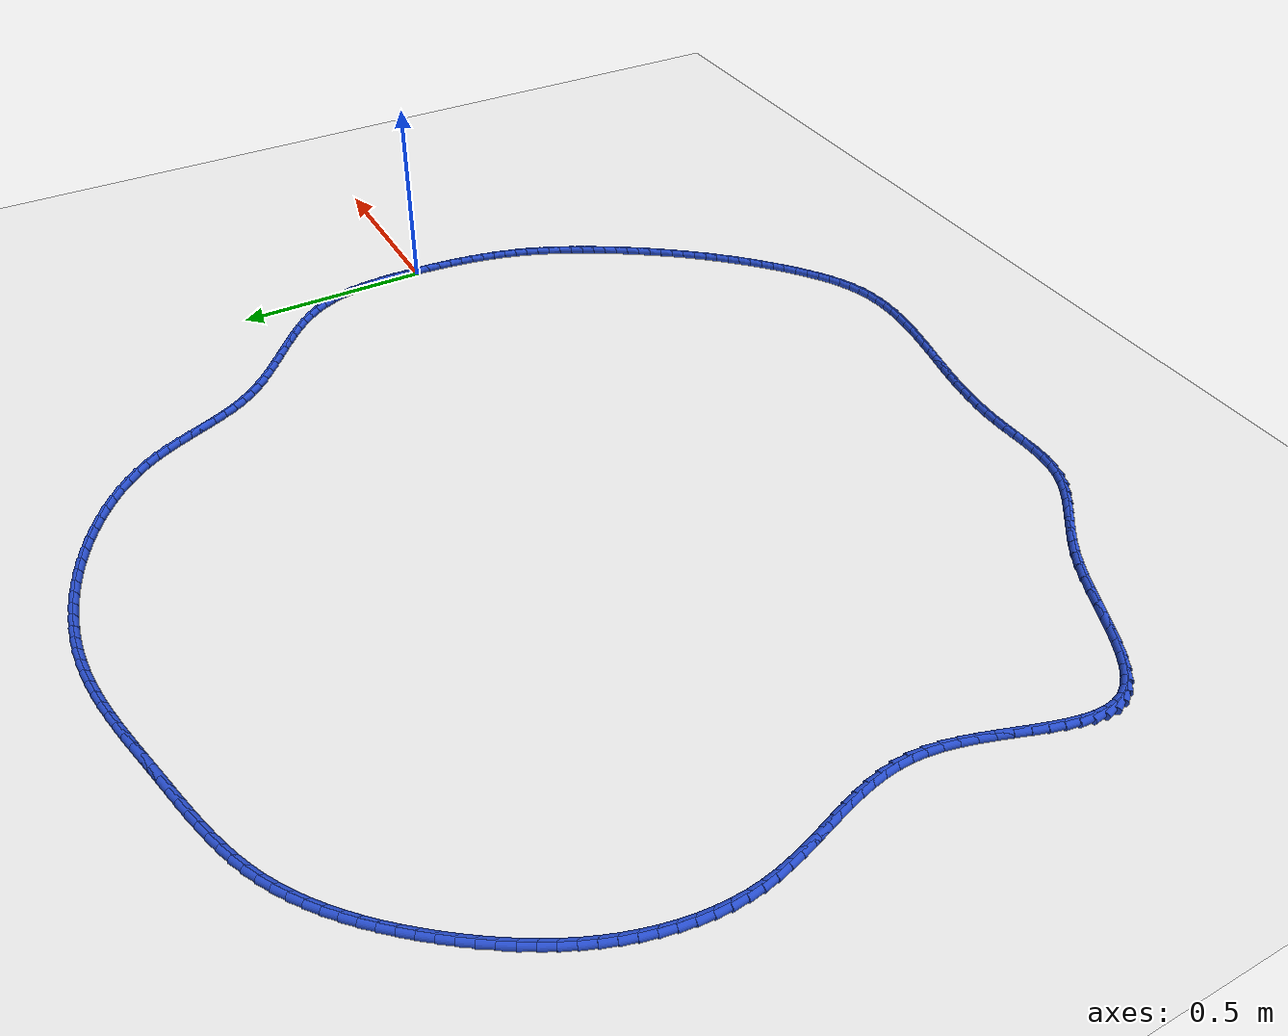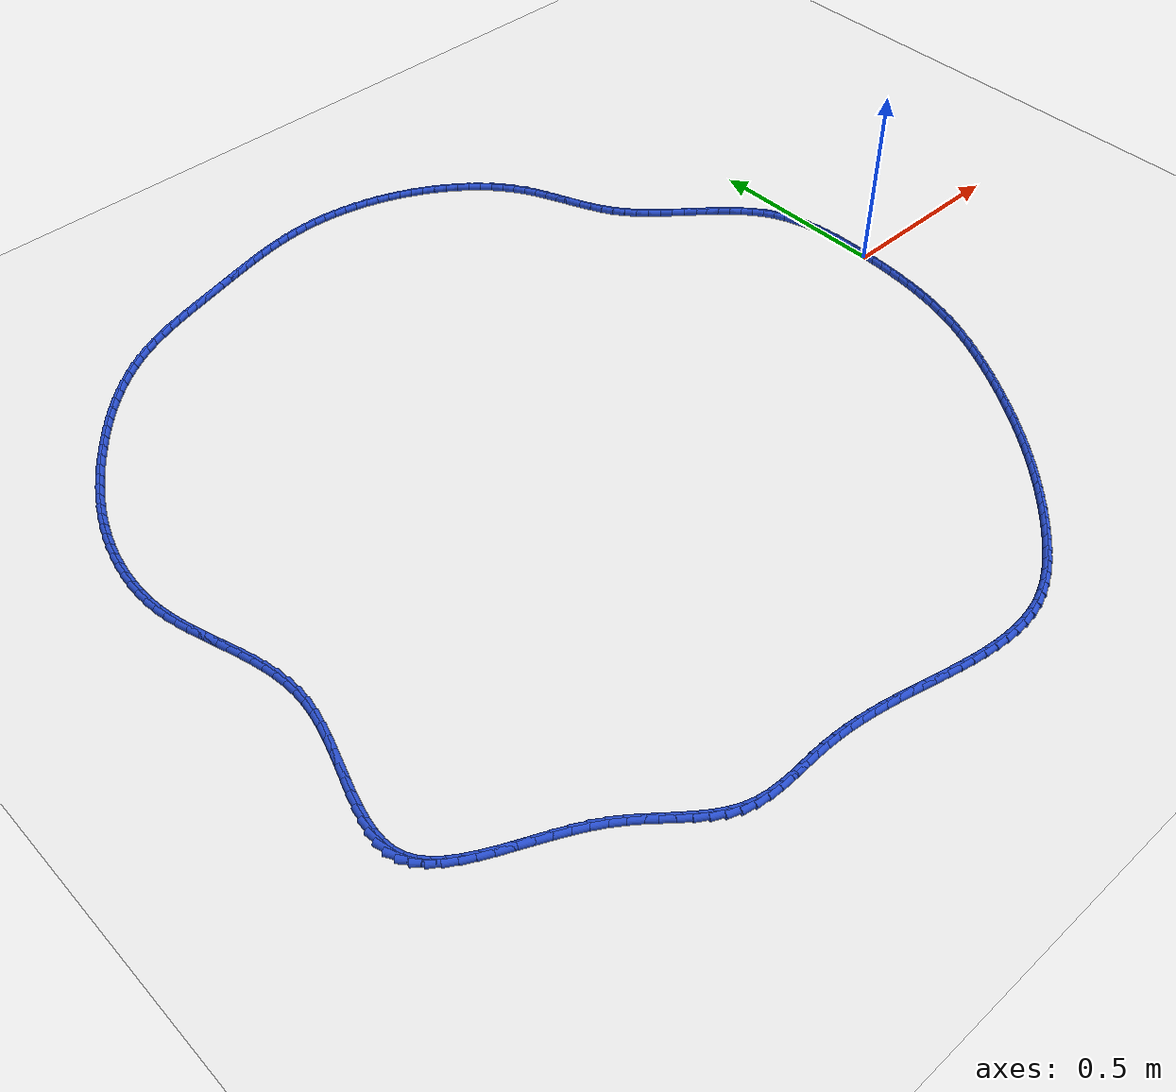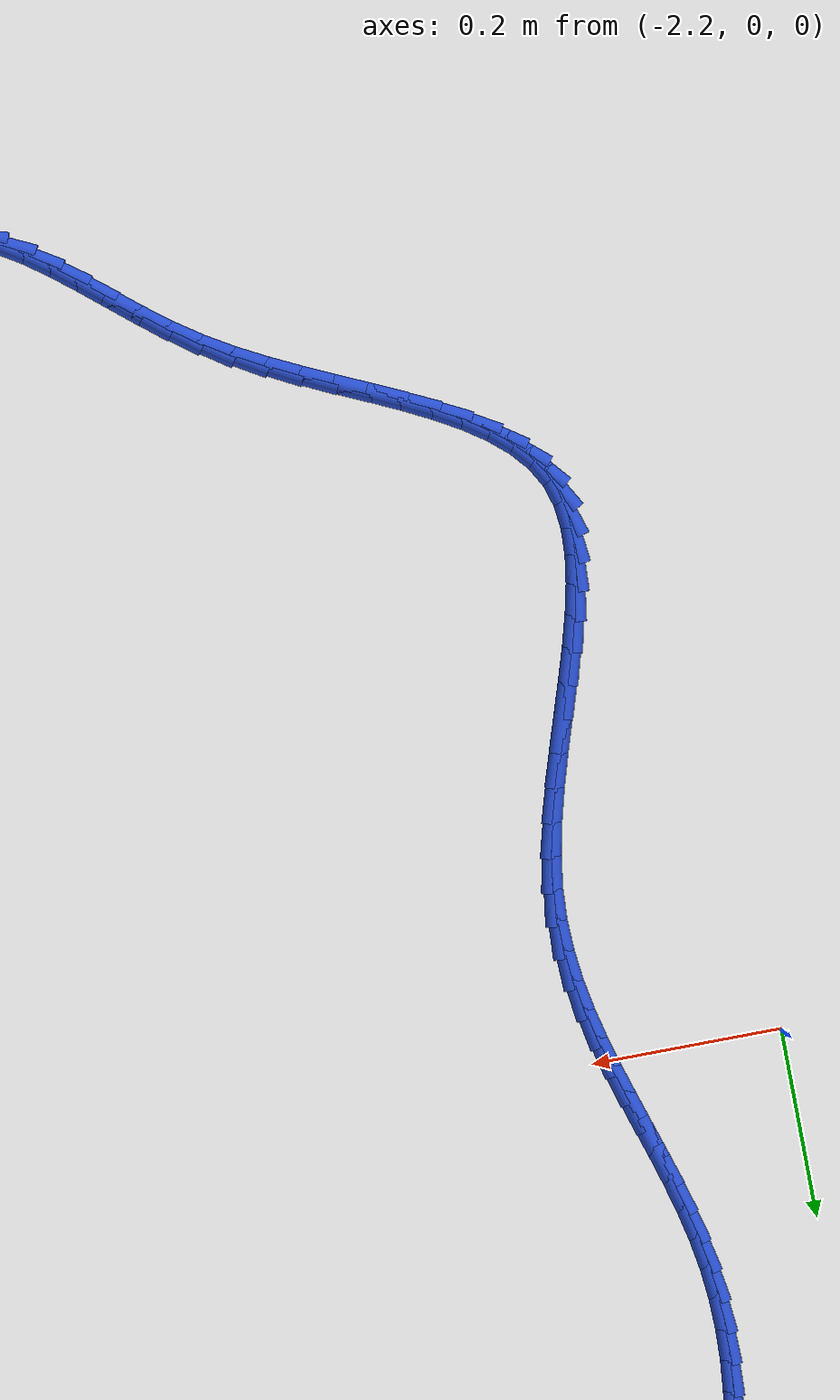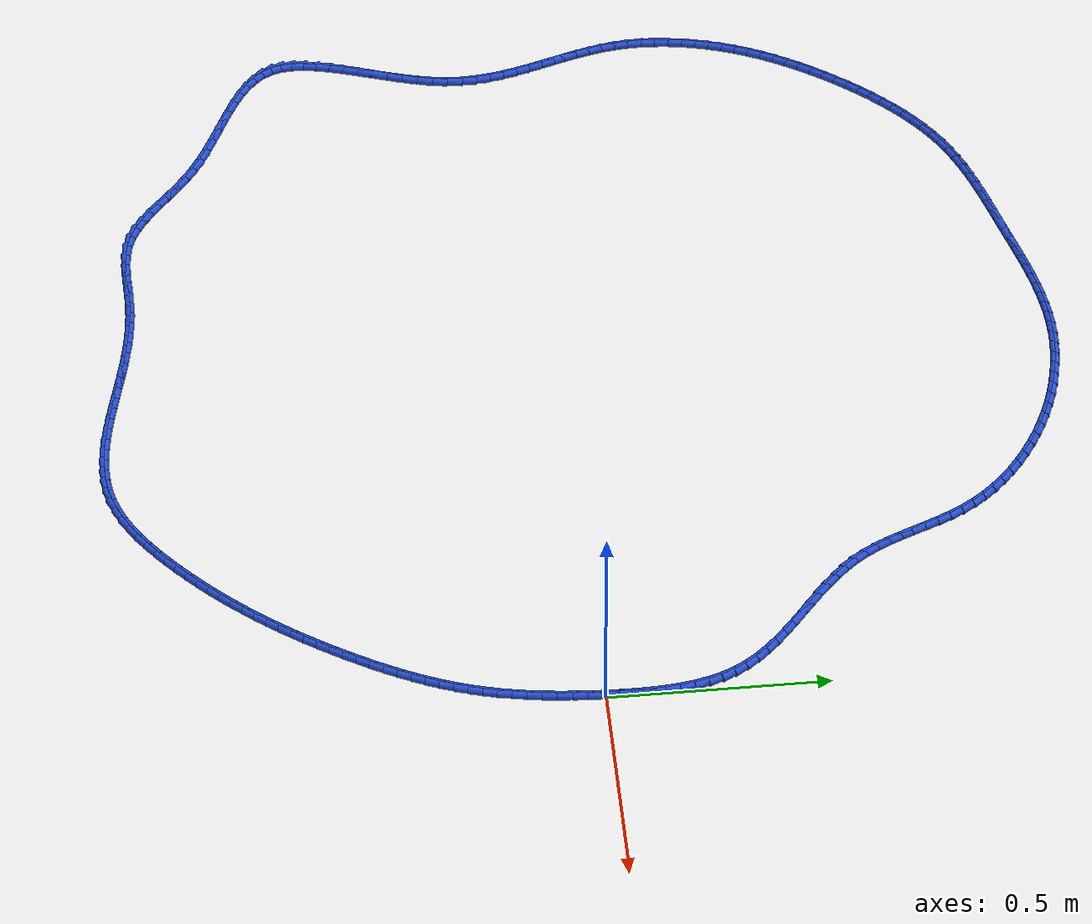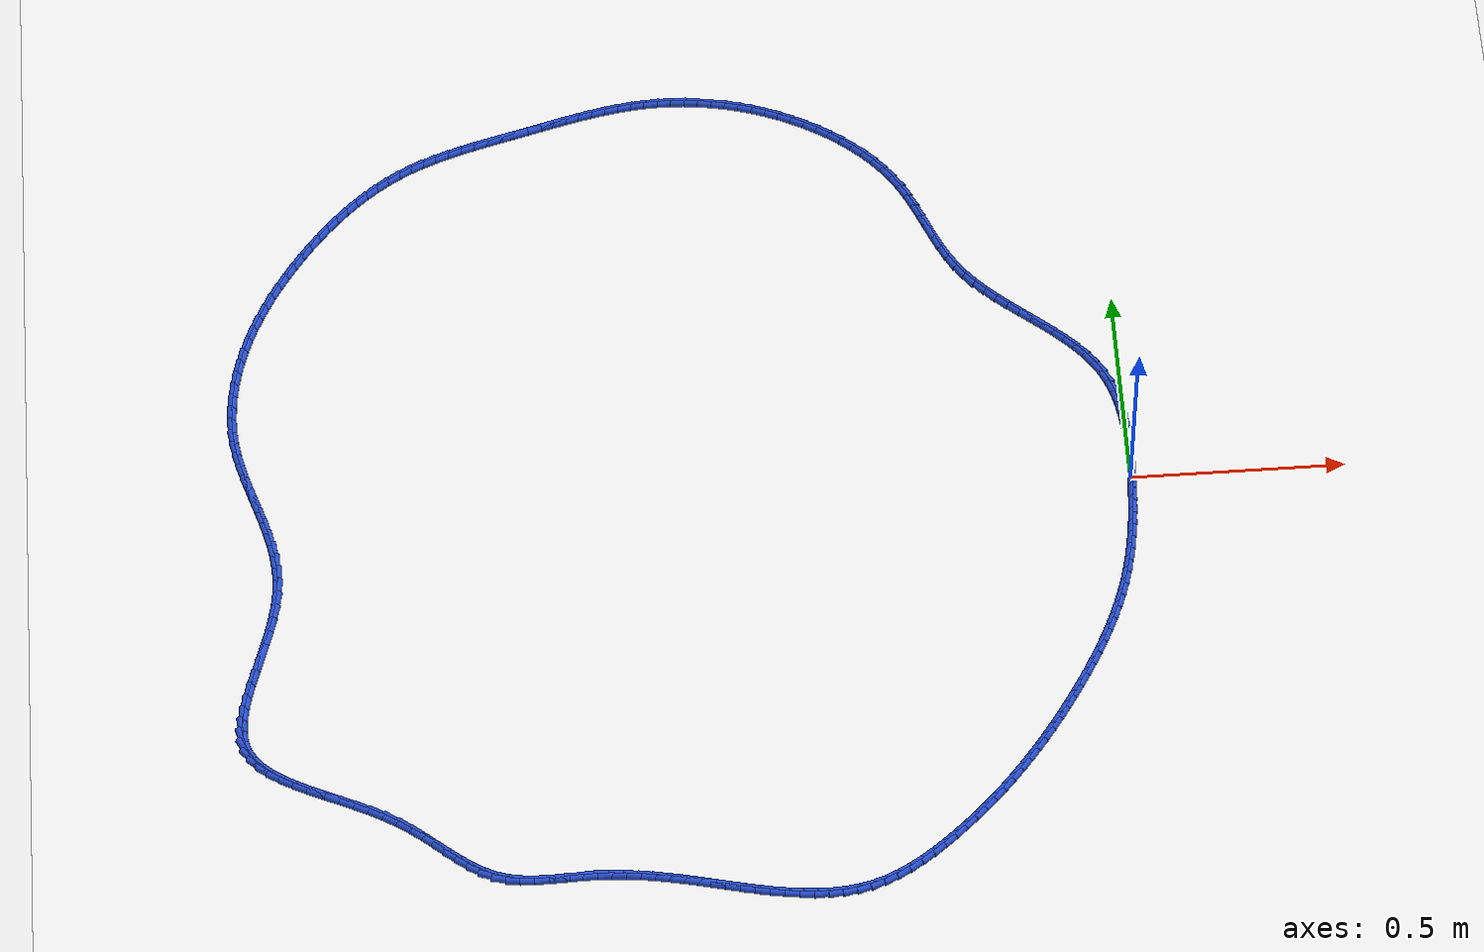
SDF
<sdf version="1.6">
 <world name="default">
  <light name="sun" type="directional">
   <pose>0 0 10 0 -0 0</pose>
   <diffuse>0.8 0.8 0.8 1</diffuse>
   <specular>0.2 0.2 0.2 1</specular>
   <attenuation>
    <range>1000</range>
    <constant>0.9</constant>
    <linear>0.01</linear>
    <quadratic>0.001</quadratic>
   </attenuation>
   <direction>-0.5 0.1 -0.9</direction>
  </light>
  <model name="ground_plane">
   <static>1</static>
   <link name="link">
    <collision name="collision">
     <geometry><plane><normal>0 0 1</normal><size>100 100</size></plane></geometry>
     <surface><friction><ode><mu>100</mu><mu2>50</mu2></ode></friction></surface>
    </collision>
    <visual name="visual">
     <cast_shadows>0</cast_shadows>
     <geometry><plane><normal>0 0 1</normal><size>100 100</size></plane></geometry>
     <material>
      <script><uri>file://media/materials/scripts/gazebo.material</uri><name>Gazebo/WhiteGlow</name></script>
     </material>
    </visual>
   </link>
  </model>
  <gravity>0 0 -9.8</gravity>
  <magnetic_field>6e-06 2.3e-05 -4.2e-05</magnetic_field>
  <atmosphere type="adiabatic"/>
  <physics name="default_physics" default="0" type="ode">
   <max_step_size>0.001</max_step_size>
   <real_time_factor>1</real_time_factor>
   <real_time_update_rate>1000</real_time_update_rate>
  </physics>
  <scene><ambient>0.4 0.4 0.4 1</ambient><background>0.7 0.7 0.7 1</background><shadows>1</shadows></scene>
  <spherical_coordinates>
   <surface_model>EARTH_WGS84</surface_model>
   <latitude_deg>0</latitude_deg>
   <longitude_deg>0</longitude_deg>
   <elevation>0</elevation>
   <heading_deg>0</heading_deg>
  </spherical_coordinates>
  <model name="line">
   <link name="link_0">
    <pose>4.445228907190568e-18 -3.469446951953614e-17 0.01 0 1.57 1.5410624673054036</pose>
    <collision name="collision">
     <geometry><cylinder><radius>0.01</radius><length>0.08</length></cylinder></geometry>
    </collision>
    <visual name="visual">
     <material>
      <script><name>Gazebo/Blue</name><uri>file://media/materials/scripts/gazebo.material</uri></script>
     </material>
     <geometry><cylinder><radius>0.01</radius><length>0.08</length></cylinder></geometry>
    </visual>
   </link>
   <link name="link_1">
    <pose>0.0010117681337784947 0.03401744558865021 0.01 0 1.57 1.5644141247974244</pose>
    <collision name="collision">
     <geometry><cylinder><radius>0.01</radius><length>0.08</length></cylinder></geometry>
    </collision>
    <visual name="visual">
     <material>
      <script><name>Gazebo/Blue</name><uri>file://media/materials/scripts/gazebo.material</uri></script>
     </material>
     <geometry><cylinder><radius>0.01</radius><length>0.08</length></cylinder></geometry>
    </visual>
   </link>
   <link name="link_2">
    <pose>0.001229728686603296 0.06816829094633647 0.01 0 1.57 -1.5457852256134852</pose>
    <collision name="collision">
     <geometry><cylinder><radius>0.01</radius><length>0.08</length></cylinder></geometry>
    </collision>
    <visual name="visual">
     <material>
      <script><name>Gazebo/Blue</name><uri>file://media/materials/scripts/gazebo.material</uri></script>
     </material>
     <geometry><cylinder><radius>0.01</radius><length>0.08</length></cylinder></geometry>
    </visual>
   </link>
   <link name="link_3">
    <pose>0.00037788111578270726 0.10221996789361065 0.01 0 1.57 -1.5057145824237133</pose>
    <collision name="collision">
     <geometry><cylinder><radius>0.01</radius><length>0.08</length></cylinder></geometry>
    </collision>
    <visual name="visual">
     <material>
      <script><name>Gazebo/Blue</name><uri>file://media/materials/scripts/gazebo.material</uri></script>
     </material>
     <geometry><cylinder><radius>0.01</radius><length>0.08</length></cylinder></geometry>
    </visual>
   </link>
   <link name="link_4">
    <pose>-0.0018197751213749704 0.1359399082510246 0.01 0 1.57 -1.456103813256212</pose>
    <collision name="collision">
     <geometry><cylinder><radius>0.01</radius><length>0.08</length></cylinder></geometry>
    </collision>
    <visual name="visual">
     <material>
      <script><name>Gazebo/Blue</name><uri>file://media/materials/scripts/gazebo.material</uri></script>
     </material>
     <geometry><cylinder><radius>0.01</radius><length>0.08</length></cylinder></geometry>
    </visual>
   </link>
   <link name="link_5">
    <pose>-0.00563924056756144 0.1690955438391303 0.01 0 1.57 -1.3959171814999916</pose>
    <collision name="collision">
     <geometry><cylinder><radius>0.01</radius><length>0.08</length></cylinder></geometry>
    </collision>
    <visual name="visual">
     <material>
      <script><name>Gazebo/Blue</name><uri>file://media/materials/scripts/gazebo.material</uri></script>
     </material>
     <geometry><cylinder><radius>0.01</radius><length>0.08</length></cylinder></geometry>
    </visual>
   </link>
   <link name="link_6">
    <pose>-0.011356515765468402 0.20145430647847976 0.01 0 1.57 -1.3240533585304117</pose>
    <collision name="collision">
     <geometry><cylinder><radius>0.01</radius><length>0.08</length></cylinder></geometry>
    </collision>
    <visual name="visual">
     <material>
      <script><name>Gazebo/Blue</name><uri>file://media/materials/scripts/gazebo.material</uri></script>
     </material>
     <geometry><cylinder><radius>0.01</radius><length>0.08</length></cylinder></geometry>
    </visual>
   </link>
   <link name="link_7">
    <pose>-0.019247601257787558 0.2327836279896246 0.01 0 1.57 -1.2395438715242892</pose>
    <collision name="collision">
     <geometry><cylinder><radius>0.01</radius><length>0.08</length></cylinder></geometry>
    </collision>
    <visual name="visual">
     <material>
      <script><name>Gazebo/Blue</name><uri>file://media/materials/scripts/gazebo.material</uri></script>
     </material>
     <geometry><cylinder><radius>0.01</radius><length>0.08</length></cylinder></geometry>
    </visual>
   </link>
   <link name="link_8">
    <pose>-0.0295884975872106 0.262850940193117 0.01 0 1.57 -1.141876861490044</pose>
    <collision name="collision">
     <geometry><cylinder><radius>0.01</radius><length>0.08</length></cylinder></geometry>
    </collision>
    <visual name="visual">
     <material>
      <script><name>Gazebo/Blue</name><uri>file://media/materials/scripts/gazebo.material</uri></script>
     </material>
     <geometry><cylinder><radius>0.01</radius><length>0.08</length></cylinder></geometry>
    </visual>
   </link>
   <link name="link_9">
    <pose>-0.04265520529642923 0.29142367490950866 0.01 0 1.57 -1.0344659712067037</pose>
    <collision name="collision">
     <geometry><cylinder><radius>0.01</radius><length>0.08</length></cylinder></geometry>
    </collision>
    <visual name="visual">
     <material>
      <script><name>Gazebo/Blue</name><uri>file://media/materials/scripts/gazebo.material</uri></script>
     </material>
     <geometry><cylinder><radius>0.01</radius><length>0.08</length></cylinder></geometry>
    </visual>
   </link>
   <link name="link_10">
    <pose>-0.05864610086537305 0.3183238894450057 0.01 0 1.57 -0.9363617559724516</pose>
    <collision name="collision">
     <geometry><cylinder><radius>0.01</radius><length>0.08</length></cylinder></geometry>
    </collision>
    <visual name="visual">
     <material>
      <script><name>Gazebo/Blue</name><uri>file://media/materials/scripts/gazebo.material</uri></script>
     </material>
     <geometry><cylinder><radius>0.01</radius><length>0.08</length></cylinder></geometry>
    </visual>
   </link>
   <link name="link_11">
    <pose>-0.07731247507242245 0.3436882635657469 0.01 0 1.57 -0.8551392113034808</pose>
    <collision name="collision">
     <geometry><cylinder><radius>0.01</radius><length>0.08</length></cylinder></geometry>
    </collision>
    <visual name="visual">
     <material>
      <script><name>Gazebo/Blue</name><uri>file://media/materials/scripts/gazebo.material</uri></script>
     </material>
     <geometry><cylinder><radius>0.01</radius><length>0.08</length></cylinder></geometry>
    </visual>
   </link>
   <link name="link_12">
    <pose>-0.09824588230256005 0.3677658864861203 0.01 0 1.57 -0.7908158787239333</pose>
    <collision name="collision">
     <geometry><cylinder><radius>0.01</radius><length>0.08</length></cylinder></geometry>
    </collision>
    <visual name="visual">
     <material>
      <script><name>Gazebo/Blue</name><uri>file://media/materials/scripts/gazebo.material</uri></script>
     </material>
     <geometry><cylinder><radius>0.01</radius><length>0.08</length></cylinder></geometry>
    </visual>
   </link>
   <link name="link_13">
    <pose>-0.12103767720075201 0.3908059879812509 0.01 0 1.57 -0.7426283027489987</pose>
    <collision name="collision">
     <geometry><cylinder><radius>0.01</radius><length>0.08</length></cylinder></geometry>
    </collision>
    <visual name="visual">
     <material>
      <script><name>Gazebo/Blue</name><uri>file://media/materials/scripts/gazebo.material</uri></script>
     </material>
     <geometry><cylinder><radius>0.01</radius><length>0.08</length></cylinder></geometry>
    </visual>
   </link>
   <link name="link_14">
    <pose>-0.14527921441196445 0.413057797826263 0.01 0 1.57 -0.7095812793869186</pose>
    <collision name="collision">
     <geometry><cylinder><radius>0.01</radius><length>0.08</length></cylinder></geometry>
    </collision>
    <visual name="visual">
     <material>
      <script><name>Gazebo/Blue</name><uri>file://media/materials/scripts/gazebo.material</uri></script>
     </material>
     <geometry><cylinder><radius>0.01</radius><length>0.08</length></cylinder></geometry>
    </visual>
   </link>
   <link name="link_15">
    <pose>-0.17056184858116324 0.4347705457962814 0.01 0 1.57 -0.6907858462596165</pose>
    <collision name="collision">
     <geometry><cylinder><radius>0.01</radius><length>0.08</length></cylinder></geometry>
    </collision>
    <visual name="visual">
     <material>
      <script><name>Gazebo/Blue</name><uri>file://media/materials/scripts/gazebo.material</uri></script>
     </material>
     <geometry><cylinder><radius>0.01</radius><length>0.08</length></cylinder></geometry>
    </visual>
   </link>
   <link name="link_16">
    <pose>-0.19647693435331462 0.4561934616664306 0.01 0 1.57 -0.6856366315431752</pose>
    <collision name="collision">
     <geometry><cylinder><radius>0.01</radius><length>0.08</length></cylinder></geometry>
    </collision>
    <visual name="visual">
     <material>
      <script><name>Gazebo/Blue</name><uri>file://media/materials/scripts/gazebo.material</uri></script>
     </material>
     <geometry><cylinder><radius>0.01</radius><length>0.08</length></cylinder></geometry>
    </visual>
   </link>
   <link name="link_17">
    <pose>-0.22261582637338462 0.4775757752118352 0.01 0 1.57 -0.6938864126937246</pose>
    <collision name="collision">
     <geometry><cylinder><radius>0.01</radius><length>0.08</length></cylinder></geometry>
    </collision>
    <visual name="visual">
     <material>
      <script><name>Gazebo/Blue</name><uri>file://media/materials/scripts/gazebo.material</uri></script>
     </material>
     <geometry><cylinder><radius>0.01</radius><length>0.08</length></cylinder></geometry>
    </visual>
   </link>
   <link name="link_18">
    <pose>-0.24856987928633936 0.49916671620762 0.01 0 1.57 -0.7156566887445555</pose>
    <collision name="collision">
     <geometry><cylinder><radius>0.01</radius><length>0.08</length></cylinder></geometry>
    </collision>
    <visual name="visual">
     <material>
      <script><name>Gazebo/Blue</name><uri>file://media/materials/scripts/gazebo.material</uri></script>
     </material>
     <geometry><cylinder><radius>0.01</radius><length>0.08</length></cylinder></geometry>
    </visual>
   </link>
   <link name="link_19">
    <pose>-0.27393044773714487 0.5212155144289095 0.01 0 1.57 -0.7513971276584475</pose>
    <collision name="collision">
     <geometry><cylinder><radius>0.01</radius><length>0.08</length></cylinder></geometry>
    </collision>
    <visual name="visual">
     <material>
      <script><name>Gazebo/Blue</name><uri>file://media/materials/scripts/gazebo.material</uri></script>
     </material>
     <geometry><cylinder><radius>0.01</radius><length>0.08</length></cylinder></geometry>
    </visual>
   </link>
   <link name="link_20">
    <pose>-0.2982888863707673 0.5439713996508284 0.01 0 1.57 -0.8017820538927554</pose>
    <collision name="collision">
     <geometry><cylinder><radius>0.01</radius><length>0.08</length></cylinder></geometry>
    </collision>
    <visual name="visual">
     <material>
      <script><name>Gazebo/Blue</name><uri>file://media/materials/scripts/gazebo.material</uri></script>
     </material>
     <geometry><cylinder><radius>0.01</radius><length>0.08</length></cylinder></geometry>
    </visual>
   </link>
   <link name="link_21">
    <pose>-0.32123654983217254 0.567683601648501 0.01 0 1.57 -0.8675113863960809</pose>
    <collision name="collision">
     <geometry><cylinder><radius>0.01</radius><length>0.08</length></cylinder></geometry>
    </collision>
    <visual name="visual">
     <material>
      <script><name>Gazebo/Blue</name><uri>file://media/materials/scripts/gazebo.material</uri></script>
     </material>
     <geometry><cylinder><radius>0.01</radius><length>0.08</length></cylinder></geometry>
    </visual>
   </link>
   <link name="link_22">
    <pose>-0.3423647927663269 0.5926013501970524 0.01 0 1.57 -0.94869707503541</pose>
    <collision name="collision">
     <geometry><cylinder><radius>0.01</radius><length>0.08</length></cylinder></geometry>
    </collision>
    <visual name="visual">
     <material>
      <script><name>Gazebo/Blue</name><uri>file://media/materials/scripts/gazebo.material</uri></script>
     </material>
     <geometry><cylinder><radius>0.01</radius><length>0.08</length></cylinder></geometry>
    </visual>
   </link>
   <link name="link_23">
    <pose>-0.36127263551704075 0.6189690710990231 0.01 0 1.57 -1.031552007737878</pose>
    <collision name="collision">
     <geometry><cylinder><radius>0.01</radius><length>0.08</length></cylinder></geometry>
    </collision>
    <visual name="visual">
     <material>
      <script><name>Gazebo/Blue</name><uri>file://media/materials/scripts/gazebo.material</uri></script>
     </material>
     <geometry><cylinder><radius>0.01</radius><length>0.08</length></cylinder></geometry>
    </visual>
   </link>
   <link name="link_24">
    <pose>-0.37792708851723267 0.6468005765710287 0.01 0 1.57 -1.0961575629234763</pose>
    <collision name="collision">
     <geometry><cylinder><radius>0.01</radius><length>0.08</length></cylinder></geometry>
    </collision>
    <visual name="visual">
     <material>
      <script><name>Gazebo/Blue</name><uri>file://media/materials/scripts/gazebo.material</uri></script>
     </material>
     <geometry><cylinder><radius>0.01</radius><length>0.08</length></cylinder></geometry>
    </visual>
   </link>
   <link name="link_25">
    <pose>-0.39281815395392383 0.6757819281445621 0.01 0 1.57 -1.1409574798711377</pose>
    <collision name="collision">
     <geometry><cylinder><radius>0.01</radius><length>0.08</length></cylinder></geometry>
    </collision>
    <visual name="visual">
     <material>
      <script><name>Gazebo/Blue</name><uri>file://media/materials/scripts/gazebo.material</uri></script>
     </material>
     <geometry><cylinder><radius>0.01</radius><length>0.08</length></cylinder></geometry>
    </visual>
   </link>
   <link name="link_26">
    <pose>-0.4064757057961559 0.7055742003340725 0.01 0 1.57 -1.1663648958755957</pose>
    <collision name="collision">
     <geometry><cylinder><radius>0.01</radius><length>0.08</length></cylinder></geometry>
    </collision>
    <visual name="visual">
     <material>
      <script><name>Gazebo/Blue</name><uri>file://media/materials/scripts/gazebo.material</uri></script>
     </material>
     <geometry><cylinder><radius>0.01</radius><length>0.08</length></cylinder></geometry>
    </visual>
   </link>
   <link name="link_27">
    <pose>-0.41942961801296946 0.7358384676540073 0.01 0 1.57 -1.172797440958279</pose>
    <collision name="collision">
     <geometry><cylinder><radius>0.01</radius><length>0.08</length></cylinder></geometry>
    </collision>
    <visual name="visual">
     <material>
      <script><name>Gazebo/Blue</name><uri>file://media/materials/scripts/gazebo.material</uri></script>
     </material>
     <geometry><cylinder><radius>0.01</radius><length>0.08</length></cylinder></geometry>
    </visual>
   </link>
   <link name="link_28">
    <pose>-0.4322097645734062 0.766235804618816 0.01 0 1.57 -1.1604037165864045</pose>
    <collision name="collision">
     <geometry><cylinder><radius>0.01</radius><length>0.08</length></cylinder></geometry>
    </collision>
    <visual name="visual">
     <material>
      <script><name>Gazebo/Blue</name><uri>file://media/materials/scripts/gazebo.material</uri></script>
     </material>
     <geometry><cylinder><radius>0.01</radius><length>0.08</length></cylinder></geometry>
    </visual>
   </link>
   <link name="link_29">
    <pose>-0.44534601944650676 0.7964272857429463 0.01 0 1.57 -1.128999042828252</pose>
    <collision name="collision">
     <geometry><cylinder><radius>0.01</radius><length>0.08</length></cylinder></geometry>
    </collision>
    <visual name="visual">
     <material>
      <script><name>Gazebo/Blue</name><uri>file://media/materials/scripts/gazebo.material</uri></script>
     </material>
     <geometry><cylinder><radius>0.01</radius><length>0.08</length></cylinder></geometry>
    </visual>
   </link>
   <link name="link_30">
    <pose>-0.45936825660131286 0.8260739855408477 0.01 0 1.57 -1.078194699756277</pose>
    <collision name="collision">
     <geometry><cylinder><radius>0.01</radius><length>0.08</length></cylinder></geometry>
    </collision>
    <visual name="visual">
     <material>
      <script><name>Gazebo/Blue</name><uri>file://media/materials/scripts/gazebo.material</uri></script>
     </material>
     <geometry><cylinder><radius>0.01</radius><length>0.08</length></cylinder></geometry>
    </visual>
   </link>
   <link name="link_31">
    <pose>-0.4748063500068654 0.8548369785269678 0.01 0 1.57 -1.0085450246367451</pose>
    <collision name="collision">
     <geometry><cylinder><radius>0.01</radius><length>0.08</length></cylinder></geometry>
    </collision>
    <visual name="visual">
     <material>
      <script><name>Gazebo/Blue</name><uri>file://media/materials/scripts/gazebo.material</uri></script>
     </material>
     <geometry><cylinder><radius>0.01</radius><length>0.08</length></cylinder></geometry>
    </visual>
   </link>
   <link name="link_32">
    <pose>-0.49216643523968895 0.8823887253139763 0.01 0 1.57 -0.9329389567857763</pose>
    <collision name="collision">
     <geometry><cylinder><radius>0.01</radius><length>0.08</length></cylinder></geometry>
    </collision>
    <visual name="visual">
     <material>
      <script><name>Gazebo/Blue</name><uri>file://media/materials/scripts/gazebo.material</uri></script>
     </material>
     <geometry><cylinder><radius>0.01</radius><length>0.08</length></cylinder></geometry>
    </visual>
   </link>
   <link name="link_33">
    <pose>-0.5115806831743348 0.908581058341203 0.01 0 1.57 -0.8616593909967866</pose>
    <collision name="collision">
     <geometry><cylinder><radius>0.01</radius><length>0.08</length></cylinder></geometry>
    </collision>
    <visual name="visual">
     <material>
      <script><name>Gazebo/Blue</name><uri>file://media/materials/scripts/gazebo.material</uri></script>
     </material>
     <geometry><cylinder><radius>0.01</radius><length>0.08</length></cylinder></geometry>
    </visual>
   </link>
   <link name="link_34">
    <pose>-0.5328834745917851 0.9334086447935108 0.01 0 1.57 -0.7949507242816893</pose>
    <collision name="collision">
     <geometry><cylinder><radius>0.01</radius><length>0.08</length></cylinder></geometry>
    </collision>
    <visual name="visual">
     <material>
      <script><name>Gazebo/Blue</name><uri>file://media/materials/scripts/gazebo.material</uri></script>
     </material>
     <geometry><cylinder><radius>0.01</radius><length>0.08</length></cylinder></geometry>
    </visual>
   </link>
   <link name="link_35">
    <pose>-0.5559009350011416 0.9568701114893574 0.01 0 1.57 -0.7326248424997793</pose>
    <collision name="collision">
     <geometry><cylinder><radius>0.01</radius><length>0.08</length></cylinder></geometry>
    </collision>
    <visual name="visual">
     <material>
      <script><name>Gazebo/Blue</name><uri>file://media/materials/scripts/gazebo.material</uri></script>
     </material>
     <geometry><cylinder><radius>0.01</radius><length>0.08</length></cylinder></geometry>
    </visual>
   </link>
   <link name="link_36">
    <pose>-0.5804591899115047 0.9789640852472004 0.01 0 1.57 -0.6743872848858621</pose>
    <collision name="collision">
     <geometry><cylinder><radius>0.01</radius><length>0.08</length></cylinder></geometry>
    </collision>
    <visual name="visual">
     <material>
      <script><name>Gazebo/Blue</name><uri>file://media/materials/scripts/gazebo.material</uri></script>
     </material>
     <geometry><cylinder><radius>0.01</radius><length>0.08</length></cylinder></geometry>
    </visual>
   </link>
   <link name="link_37">
    <pose>-0.6063843648319763 0.9996891928854968 0.01 0 1.57 -0.6198760626431113</pose>
    <collision name="collision">
     <geometry><cylinder><radius>0.01</radius><length>0.08</length></cylinder></geometry>
    </collision>
    <visual name="visual">
     <material>
      <script><name>Gazebo/Blue</name><uri>file://media/materials/scripts/gazebo.material</uri></script>
     </material>
     <geometry><cylinder><radius>0.01</radius><length>0.08</length></cylinder></geometry>
    </visual>
   </link>
   <link name="link_38">
    <pose>-0.6335025852716571 1.0190440612227045 0.01 0 1.57 -0.5686908266370944</pose>
    <collision name="collision">
     <geometry><cylinder><radius>0.01</radius><length>0.08</length></cylinder></geometry>
    </collision>
    <visual name="visual">
     <material>
      <script><name>Gazebo/Blue</name><uri>file://media/materials/scripts/gazebo.material</uri></script>
     </material>
     <geometry><cylinder><radius>0.01</radius><length>0.08</length></cylinder></geometry>
    </visual>
   </link>
   <link name="link_39">
    <pose>-0.6616399767396481 1.0370273170772806 0.01 0 1.57 -0.5202596841059057</pose>
    <collision name="collision">
     <geometry><cylinder><radius>0.01</radius><length>0.08</length></cylinder></geometry>
    </collision>
    <visual name="visual">
     <material>
      <script><name>Gazebo/Blue</name><uri>file://media/materials/scripts/gazebo.material</uri></script>
     </material>
     <geometry><cylinder><radius>0.01</radius><length>0.08</length></cylinder></geometry>
    </visual>
   </link>
   <link name="link_40">
    <pose>-0.6906298716489333 1.0536358220195037 0.01 0 1.57 -0.4730301392752149</pose>
    <collision name="collision">
     <geometry><cylinder><radius>0.01</radius><length>0.08</length></cylinder></geometry>
    </collision>
    <visual name="visual">
     <material>
      <script><name>Gazebo/Blue</name><uri>file://media/materials/scripts/gazebo.material</uri></script>
     </material>
     <geometry><cylinder><radius>0.01</radius><length>0.08</length></cylinder></geometry>
    </visual>
   </link>
   <link name="link_41">
    <pose>-0.720362502618153 1.0688525005690028 0.01 0 1.57 -0.42625510700309627</pose>
    <collision name="collision">
     <geometry><cylinder><radius>0.01</radius><length>0.08</length></cylinder></geometry>
    </collision>
    <visual name="visual">
     <material>
      <script><name>Gazebo/Blue</name><uri>file://media/materials/scripts/gazebo.material</uri></script>
     </material>
     <geometry><cylinder><radius>0.01</radius><length>0.08</length></cylinder></geometry>
    </visual>
   </link>
   <link name="link_42">
    <pose>-0.7507551010814724 1.0826536641962077 0.01 0 1.57 -0.3797806625369157</pose>
    <collision name="collision">
     <geometry><cylinder><radius>0.01</radius><length>0.08</length></cylinder></geometry>
    </collision>
    <visual name="visual">
     <material>
      <script><name>Gazebo/Blue</name><uri>file://media/materials/scripts/gazebo.material</uri></script>
     </material>
     <geometry><cylinder><radius>0.01</radius><length>0.08</length></cylinder></geometry>
    </visual>
   </link>
   <link name="link_43">
    <pose>-0.7817250613803163 1.0950155844692906 0.01 0 1.57 -0.3334519173002652</pose>
    <collision name="collision">
     <geometry><cylinder><radius>0.01</radius><length>0.08</length></cylinder></geometry>
    </collision>
    <visual name="visual">
     <material>
      <script><name>Gazebo/Blue</name><uri>file://media/materials/scripts/gazebo.material</uri></script>
     </material>
     <geometry><cylinder><radius>0.01</radius><length>0.08</length></cylinder></geometry>
    </visual>
   </link>
   <link name="link_44">
    <pose>-0.8131897778561092 1.1059145329564224 0.01 0 1.57 -0.28711072744376104</pose>
    <collision name="collision">
     <geometry><cylinder><radius>0.01</radius><length>0.08</length></cylinder></geometry>
    </collision>
    <visual name="visual">
     <material>
      <script><name>Gazebo/Blue</name><uri>file://media/materials/scripts/gazebo.material</uri></script>
     </material>
     <geometry><cylinder><radius>0.01</radius><length>0.08</length></cylinder></geometry>
    </visual>
   </link>
   <link name="link_45">
    <pose>-0.8450666448502755 1.1153267812257748 0.01 0 1.57 -0.24059673787612978</pose>
    <collision name="collision">
     <geometry><cylinder><radius>0.01</radius><length>0.08</length></cylinder></geometry>
    </collision>
    <visual name="visual">
     <material>
      <script><name>Gazebo/Blue</name><uri>file://media/materials/scripts/gazebo.material</uri></script>
     </material>
     <geometry><cylinder><radius>0.01</radius><length>0.08</length></cylinder></geometry>
    </visual>
   </link>
   <link name="link_46">
    <pose>-0.8772730567042402 1.12322860084552 0.01 0 1.57 -0.19374840617515232</pose>
    <collision name="collision">
     <geometry><cylinder><radius>0.01</radius><length>0.08</length></cylinder></geometry>
    </collision>
    <visual name="visual">
     <material>
      <script><name>Gazebo/Blue</name><uri>file://media/materials/scripts/gazebo.material</uri></script>
     </material>
     <geometry><cylinder><radius>0.01</radius><length>0.08</length></cylinder></geometry>
    </visual>
   </link>
   <link name="link_47">
    <pose>-0.9097264077594276 1.1295962633838286 0.01 0 1.57 -0.14640411665512928</pose>
    <collision name="collision">
     <geometry><cylinder><radius>0.01</radius><length>0.08</length></cylinder></geometry>
    </collision>
    <visual name="visual">
     <material>
      <script><name>Gazebo/Blue</name><uri>file://media/materials/scripts/gazebo.material</uri></script>
     </material>
     <geometry><cylinder><radius>0.01</radius><length>0.08</length></cylinder></geometry>
    </visual>
   </link>
   <link name="link_48">
    <pose>-0.9423440923572627 1.1344060404088727 0.01 0 1.57 -0.09840350027459845</pose>
    <collision name="collision">
     <geometry><cylinder><radius>0.01</radius><length>0.08</length></cylinder></geometry>
    </collision>
    <visual name="visual">
     <material>
      <script><name>Gazebo/Blue</name><uri>file://media/materials/scripts/gazebo.material</uri></script>
     </material>
     <geometry><cylinder><radius>0.01</radius><length>0.08</length></cylinder></geometry>
    </visual>
   </link>
   <link name="link_49">
    <pose>-0.9750435048391698 1.1376342034888238 0.01 0 1.57 -0.0495890805436805</pose>
    <collision name="collision">
     <geometry><cylinder><radius>0.01</radius><length>0.08</length></cylinder></geometry>
    </collision>
    <visual name="visual">
     <material>
      <script><name>Gazebo/Blue</name><uri>file://media/materials/scripts/gazebo.material</uri></script>
     </material>
     <geometry><cylinder><radius>0.01</radius><length>0.08</length></cylinder></geometry>
    </visual>
   </link>
   <link name="link_50">
    <pose>-1.0077420395465735 1.1392570241918534 0.01 0 1.57 0.00019163255612353897</pose>
    <collision name="collision">
     <geometry><cylinder><radius>0.01</radius><length>0.08</length></cylinder></geometry>
    </collision>
    <visual name="visual">
     <material>
      <script><name>Gazebo/Blue</name><uri>file://media/materials/scripts/gazebo.material</uri></script>
     </material>
     <geometry><cylinder><radius>0.01</radius><length>0.08</length></cylinder></geometry>
    </visual>
   </link>
   <link name="link_51">
    <pose>-1.0403570908208986 1.139250774086133 0.01 0 1.57 0.05039946119216887</pose>
    <collision name="collision">
     <geometry><cylinder><radius>0.01</radius><length>0.08</length></cylinder></geometry>
    </collision>
    <visual name="visual">
     <material>
      <script><name>Gazebo/Blue</name><uri>file://media/materials/scripts/gazebo.material</uri></script>
     </material>
     <geometry><cylinder><radius>0.01</radius><length>0.08</length></cylinder></geometry>
    </visual>
   </link>
   <link name="link_52">
    <pose>-1.0728175806358928 1.137613396283708 0.01 0 1.57 0.09688881395748895</pose>
    <collision name="collision">
     <geometry><cylinder><radius>0.01</radius><length>0.08</length></cylinder></geometry>
    </collision>
    <visual name="visual">
     <material>
      <script><name>Gazebo/Blue</name><uri>file://media/materials/scripts/gazebo.material</uri></script>
     </material>
     <geometry><cylinder><radius>0.01</radius><length>0.08</length></cylinder></geometry>
    </visual>
   </link>
   <link name="link_53">
    <pose>-1.105122003650213 1.1344736281005992 0.01 0 1.57 0.13788859822676158</pose>
    <collision name="collision">
     <geometry><cylinder><radius>0.01</radius><length>0.08</length></cylinder></geometry>
    </collision>
    <visual name="visual">
     <material>
      <script><name>Gazebo/Blue</name><uri>file://media/materials/scripts/gazebo.material</uri></script>
     </material>
     <geometry><cylinder><radius>0.01</radius><length>0.08</length></cylinder></geometry>
    </visual>
   </link>
   <link name="link_54">
    <pose>-1.1372948254822375 1.1300090313449087 0.01 0 1.57 0.17325404245516116</pose>
    <collision name="collision">
     <geometry><cylinder><radius>0.01</radius><length>0.08</length></cylinder></geometry>
    </collision>
    <visual name="visual">
     <material>
      <script><name>Gazebo/Blue</name><uri>file://media/materials/scripts/gazebo.material</uri></script>
     </material>
     <geometry><cylinder><radius>0.01</radius><length>0.08</length></cylinder></geometry>
    </visual>
   </link>
   <link name="link_55">
    <pose>-1.1693605563325442 1.1243972516377043 0.01 0 1.57 0.20294175754099097</pose>
    <collision name="collision">
     <geometry><cylinder><radius>0.01</radius><length>0.08</length></cylinder></geometry>
    </collision>
    <visual name="visual">
     <material>
      <script><name>Gazebo/Blue</name><uri>file://media/materials/scripts/gazebo.material</uri></script>
     </material>
     <geometry><cylinder><radius>0.01</radius><length>0.08</length></cylinder></geometry>
    </visual>
   </link>
   <link name="link_56">
    <pose>-1.2013437064017087 1.1178159346000511 0.01 0 1.57 0.2269737903030332</pose>
    <collision name="collision">
     <geometry><cylinder><radius>0.01</radius><length>0.08</length></cylinder></geometry>
    </collision>
    <visual name="visual">
     <material>
      <script><name>Gazebo/Blue</name><uri>file://media/materials/scripts/gazebo.material</uri></script>
     </material>
     <geometry><cylinder><radius>0.01</radius><length>0.08</length></cylinder></geometry>
    </visual>
   </link>
   <link name="link_57">
    <pose>-1.2332687858903064 1.1104427258530152 0.01 0 1.57 0.24540875320758465</pose>
    <collision name="collision">
     <geometry><cylinder><radius>0.01</radius><length>0.08</length></cylinder></geometry>
    </collision>
    <visual name="visual">
     <material>
      <script><name>Gazebo/Blue</name><uri>file://media/materials/scripts/gazebo.material</uri></script>
     </material>
     <geometry><cylinder><radius>0.01</radius><length>0.08</length></cylinder></geometry>
    </visual>
   </link>
   <link name="link_58">
    <pose>-1.265160304998914 1.1024552710176632 0.01 0 1.57 0.258318804709631</pose>
    <collision name="collision">
     <geometry><cylinder><radius>0.01</radius><length>0.08</length></cylinder></geometry>
    </collision>
    <visual name="visual">
     <material>
      <script><name>Gazebo/Blue</name><uri>file://media/materials/scripts/gazebo.material</uri></script>
     </material>
     <geometry><cylinder><radius>0.01</radius><length>0.08</length></cylinder></geometry>
    </visual>
   </link>
   <link name="link_59">
    <pose>-1.2970427739281072 1.0940312157150605 0.01 0 1.57 0.26577271081590753</pose>
    <collision name="collision">
     <geometry><cylinder><radius>0.01</radius><length>0.08</length></cylinder></geometry>
    </collision>
    <visual name="visual">
     <material>
      <script><name>Gazebo/Blue</name><uri>file://media/materials/scripts/gazebo.material</uri></script>
     </material>
     <geometry><cylinder><radius>0.01</radius><length>0.08</length></cylinder></geometry>
    </visual>
   </link>
   <link name="link_60">
    <pose>-1.3289407028784626 1.0853482055662735 0.01 0 1.57 0.2678246117012308</pose>
    <collision name="collision">
     <geometry><cylinder><radius>0.01</radius><length>0.08</length></cylinder></geometry>
    </collision>
    <visual name="visual">
     <material>
      <script><name>Gazebo/Blue</name><uri>file://media/materials/scripts/gazebo.material</uri></script>
     </material>
     <geometry><cylinder><radius>0.01</radius><length>0.08</length></cylinder></geometry>
    </visual>
   </link>
   <link name="link_61">
    <pose>-1.3608786020505554 1.0765838861923682 0.01 0 1.57 0.26490346352238087</pose>
    <collision name="collision">
     <geometry><cylinder><radius>0.01</radius><length>0.08</length></cylinder></geometry>
    </collision>
    <visual name="visual">
     <material>
      <script><name>Gazebo/Blue</name><uri>file://media/materials/scripts/gazebo.material</uri></script>
     </material>
     <geometry><cylinder><radius>0.01</radius><length>0.08</length></cylinder></geometry>
    </visual>
   </link>
   <link name="link_62">
    <pose>-1.3928767919007268 1.0679034520990252 0.01 0 1.57 0.26329984823263525</pose>
    <collision name="collision">
     <geometry><cylinder><radius>0.01</radius><length>0.08</length></cylinder></geometry>
    </collision>
    <visual name="visual">
     <material>
      <script><name>Gazebo/Blue</name><uri>file://media/materials/scripts/gazebo.material</uri></script>
     </material>
     <geometry><cylinder><radius>0.01</radius><length>0.08</length></cylinder></geometry>
    </visual>
   </link>
   <link name="link_63">
    <pose>-1.4248890332738946 1.059274295407003 0.01 0 1.57 0.2680458417435618</pose>
    <collision name="collision">
     <geometry><cylinder><radius>0.01</radius><length>0.08</length></cylinder></geometry>
    </collision>
    <visual name="visual">
     <material>
      <script><name>Gazebo/Blue</name><uri>file://media/materials/scripts/gazebo.material</uri></script>
     </material>
     <geometry><cylinder><radius>0.01</radius><length>0.08</length></cylinder></geometry>
    </visual>
   </link>
   <link name="link_64">
    <pose>-1.4568157956872474 1.0505054366436206 0.01 0 1.57 0.2793286706221039</pose>
    <collision name="collision">
     <geometry><cylinder><radius>0.01</radius><length>0.08</length></cylinder></geometry>
    </collision>
    <visual name="visual">
     <material>
      <script><name>Gazebo/Blue</name><uri>file://media/materials/scripts/gazebo.material</uri></script>
     </material>
     <geometry><cylinder><radius>0.01</radius><length>0.08</length></cylinder></geometry>
    </visual>
   </link>
   <link name="link_65">
    <pose>-1.4885560537555766 1.0414014537733083 0.01 0 1.57 0.29724277095952634</pose>
    <collision name="collision">
     <geometry><cylinder><radius>0.01</radius><length>0.08</length></cylinder></geometry>
    </collision>
    <visual name="visual">
     <material>
      <script><name>Gazebo/Blue</name><uri>file://media/materials/scripts/gazebo.material</uri></script>
     </material>
     <geometry><cylinder><radius>0.01</radius><length>0.08</length></cylinder></geometry>
    </visual>
   </link>
   <link name="link_66">
    <pose>-1.5200087820936747 1.0317669247604964 0.01 0 1.57 0.32191779578032237</pose>
    <collision name="collision">
     <geometry><cylinder><radius>0.01</radius><length>0.08</length></cylinder></geometry>
    </collision>
    <visual name="visual">
     <material>
      <script><name>Gazebo/Blue</name><uri>file://media/materials/scripts/gazebo.material</uri></script>
     </material>
     <geometry><cylinder><radius>0.01</radius><length>0.08</length></cylinder></geometry>
    </visual>
   </link>
   <link name="link_67">
    <pose>-1.551072955316332 1.0214064275696155 0.01 0 1.57 0.3534960953901173</pose>
    <collision name="collision">
     <geometry><cylinder><radius>0.01</radius><length>0.08</length></cylinder></geometry>
    </collision>
    <visual name="visual">
     <material>
      <script><name>Gazebo/Blue</name><uri>file://media/materials/scripts/gazebo.material</uri></script>
     </material>
     <geometry><cylinder><radius>0.01</radius><length>0.08</length></cylinder></geometry>
    </visual>
   </link>
   <link name="link_68">
    <pose>-1.5816475480383407 1.010124540165096 0.01 0 1.57 0.39209900973172196</pose>
    <collision name="collision">
     <geometry><cylinder><radius>0.01</radius><length>0.08</length></cylinder></geometry>
    </collision>
    <visual name="visual">
     <material>
      <script><name>Gazebo/Blue</name><uri>file://media/materials/scripts/gazebo.material</uri></script>
     </material>
     <geometry><cylinder><radius>0.01</radius><length>0.08</length></cylinder></geometry>
    </visual>
   </link>
   <link name="link_69">
    <pose>-1.6116315348744923 0.9977258405113676 0.01 0 1.57 0.4377806223246309</pose>
    <collision name="collision">
     <geometry><cylinder><radius>0.01</radius><length>0.08</length></cylinder></geometry>
    </collision>
    <visual name="visual">
     <material>
      <script><name>Gazebo/Blue</name><uri>file://media/materials/scripts/gazebo.material</uri></script>
     </material>
     <geometry><cylinder><radius>0.01</radius><length>0.08</length></cylinder></geometry>
    </visual>
   </link>
   <link name="link_70">
    <pose>-1.6409238904395784 0.9840149065728618 0.01 0 1.57 0.49045930680570843</pose>
    <collision name="collision">
     <geometry><cylinder><radius>0.01</radius><length>0.08</length></cylinder></geometry>
    </collision>
    <visual name="visual">
     <material>
      <script><name>Gazebo/Blue</name><uri>file://media/materials/scripts/gazebo.material</uri></script>
     </material>
     <geometry><cylinder><radius>0.01</radius><length>0.08</length></cylinder></geometry>
    </visual>
   </link>
   <link name="link_71">
    <pose>-1.669423702078045 0.9687966263965939 0.01 0 1.57 0.5471418355182243</pose>
    <collision name="collision">
     <geometry><cylinder><radius>0.01</radius><length>0.08</length></cylinder></geometry>
    </collision>
    <visual name="visual">
     <material>
      <script><name>Gazebo/Blue</name><uri>file://media/materials/scripts/gazebo.material</uri></script>
     </material>
     <geometry><cylinder><radius>0.01</radius><length>0.08</length></cylinder></geometry>
    </visual>
   </link>
   <link name="link_72">
    <pose>-1.6970608655327308 0.9519606319047175 0.01 0 1.57 0.6011597167612089</pose>
    <collision name="collision">
     <geometry><cylinder><radius>0.01</radius><length>0.08</length></cylinder></geometry>
    </collision>
    <visual name="visual">
     <material>
      <script><name>Gazebo/Blue</name><uri>file://media/materials/scripts/gazebo.material</uri></script>
     </material>
     <geometry><cylinder><radius>0.01</radius><length>0.08</length></cylinder></geometry>
    </visual>
   </link>
   <link name="link_73">
    <pose>-1.7238377643990959 0.9335959455055023 0.01 0 1.57 0.651563162706398</pose>
    <collision name="collision">
     <geometry><cylinder><radius>0.01</radius><length>0.08</length></cylinder></geometry>
    </collision>
    <visual name="visual">
     <material>
      <script><name>Gazebo/Blue</name><uri>file://media/materials/scripts/gazebo.material</uri></script>
     </material>
     <geometry><cylinder><radius>0.01</radius><length>0.08</length></cylinder></geometry>
    </visual>
   </link>
   <link name="link_74">
    <pose>-1.7497671992046833 0.9138202431964282 0.01 0 1.57 0.6984129220808186</pose>
    <collision name="collision">
     <geometry><cylinder><radius>0.01</radius><length>0.08</length></cylinder></geometry>
    </collision>
    <visual name="visual">
     <material>
      <script><name>Gazebo/Blue</name><uri>file://media/materials/scripts/gazebo.material</uri></script>
     </material>
     <geometry><cylinder><radius>0.01</radius><length>0.08</length></cylinder></geometry>
    </visual>
   </link>
   <link name="link_75">
    <pose>-1.7748619704770363 0.8927512009749745 0.01 0 1.57 0.7418250266413672</pose>
    <collision name="collision">
     <geometry><cylinder><radius>0.01</radius><length>0.08</length></cylinder></geometry>
    </collision>
    <visual name="visual">
     <material>
      <script><name>Gazebo/Blue</name><uri>file://media/materials/scripts/gazebo.material</uri></script>
     </material>
     <geometry><cylinder><radius>0.01</radius><length>0.08</length></cylinder></geometry>
    </visual>
   </link>
   <link name="link_76">
    <pose>-1.7991348787436974 0.87050649483862 0.01 0 1.57 0.7819523002345278</pose>
    <collision name="collision">
     <geometry><cylinder><radius>0.01</radius><length>0.08</length></cylinder></geometry>
    </collision>
    <visual name="visual">
     <material>
      <script><name>Gazebo/Blue</name><uri>file://media/materials/scripts/gazebo.material</uri></script>
     </material>
     <geometry><cylinder><radius>0.01</radius><length>0.08</length></cylinder></geometry>
    </visual>
   </link>
   <link name="link_77">
    <pose>-1.8225987245322093 0.8472038007848455 0.01 0 1.57 0.8189690535020485</pose>
    <collision name="collision">
     <geometry><cylinder><radius>0.01</radius><length>0.08</length></cylinder></geometry>
    </collision>
    <visual name="visual">
     <material>
      <script><name>Gazebo/Blue</name><uri>file://media/materials/scripts/gazebo.material</uri></script>
     </material>
     <geometry><cylinder><radius>0.01</radius><length>0.08</length></cylinder></geometry>
    </visual>
   </link>
   <link name="link_78">
    <pose>-1.8452663083701153 0.8229607948111292 0.01 0 1.57 0.8530590569191054</pose>
    <collision name="collision">
     <geometry><cylinder><radius>0.01</radius><length>0.08</length></cylinder></geometry>
    </collision>
    <visual name="visual">
     <material>
      <script><name>Gazebo/Blue</name><uri>file://media/materials/scripts/gazebo.material</uri></script>
     </material>
     <geometry><cylinder><radius>0.01</radius><length>0.08</length></cylinder></geometry>
    </visual>
   </link>
   <link name="link_79">
    <pose>-1.8671504307849591 0.7978951529149511 0.01 0 1.57 0.8844064954097625</pose>
    <collision name="collision">
     <geometry><cylinder><radius>0.01</radius><length>0.08</length></cylinder></geometry>
    </collision>
    <visual name="visual">
     <material>
      <script><name>Gazebo/Blue</name><uri>file://media/materials/scripts/gazebo.material</uri></script>
     </material>
     <geometry><cylinder><radius>0.01</radius><length>0.08</length></cylinder></geometry>
    </visual>
   </link>
   <link name="link_80">
    <pose>-1.8882638923042823 0.7721245510937905 0.01 0 1.57 0.913189422791282</pose>
    <collision name="collision">
     <geometry><cylinder><radius>0.01</radius><length>0.08</length></cylinder></geometry>
    </collision>
    <visual name="visual">
     <material>
      <script><name>Gazebo/Blue</name><uri>file://media/materials/scripts/gazebo.material</uri></script>
     </material>
     <geometry><cylinder><radius>0.01</radius><length>0.08</length></cylinder></geometry>
    </visual>
   </link>
   <link name="link_81">
    <pose>-1.908619493455628 0.7457666653451269 0.01 0 1.57 0.9396891827721153</pose>
    <collision name="collision">
     <geometry><cylinder><radius>0.01</radius><length>0.08</length></cylinder></geometry>
    </collision>
    <visual name="visual">
     <material>
      <script><name>Gazebo/Blue</name><uri>file://media/materials/scripts/gazebo.material</uri></script>
     </material>
     <geometry><cylinder><radius>0.01</radius><length>0.08</length></cylinder></geometry>
    </visual>
   </link>
   <link name="link_82">
    <pose>-1.9282277888019796 0.7189358245520383 0.01 0 1.57 0.9663573533749461</pose>
    <collision name="collision">
     <geometry><cylinder><radius>0.01</radius><length>0.08</length></cylinder></geometry>
    </collision>
    <visual name="visual">
     <material>
      <script><name>Gazebo/Blue</name><uri>file://media/materials/scripts/gazebo.material</uri></script>
     </material>
     <geometry><cylinder><radius>0.01</radius><length>0.08</length></cylinder></geometry>
    </visual>
   </link>
   <link name="link_83">
    <pose>-1.9470537481024932 0.691678423509938 0.01 0 1.57 0.9954213637195964</pose>
    <collision name="collision">
     <geometry><cylinder><radius>0.01</radius><length>0.08</length></cylinder></geometry>
    </collision>
    <visual name="visual">
     <material>
      <script><name>Gazebo/Blue</name><uri>file://media/materials/scripts/gazebo.material</uri></script>
     </material>
     <geometry><cylinder><radius>0.01</radius><length>0.08</length></cylinder></geometry>
    </visual>
   </link>
   <link name="link_84">
    <pose>-1.965019894553194 0.6639775997815843 0.01 0 1.57 1.027012366018567</pose>
    <collision name="collision">
     <geometry><cylinder><radius>0.01</radius><length>0.08</length></cylinder></geometry>
    </collision>
    <visual name="visual">
     <material>
      <script><name>Gazebo/Blue</name><uri>file://media/materials/scripts/gazebo.material</uri></script>
     </material>
     <geometry><cylinder><radius>0.01</radius><length>0.08</length></cylinder></geometry>
    </visual>
   </link>
   <link name="link_85">
    <pose>-1.982047134034897 0.6358140806784229 0.01 0 1.57 1.06116506006598</pose>
    <collision name="collision">
     <geometry><cylinder><radius>0.01</radius><length>0.08</length></cylinder></geometry>
    </collision>
    <visual name="visual">
     <material>
      <script><name>Gazebo/Blue</name><uri>file://media/materials/scripts/gazebo.material</uri></script>
     </material>
     <geometry><cylinder><radius>0.01</radius><length>0.08</length></cylinder></geometry>
    </visual>
   </link>
   <link name="link_86">
    <pose>-1.9980563724284144 0.6071685935118993 0.01 0 1.57 1.097893426994749</pose>
    <collision name="collision">
     <geometry><cylinder><radius>0.01</radius><length>0.08</length></cylinder></geometry>
    </collision>
    <visual name="visual">
     <material>
      <script><name>Gazebo/Blue</name><uri>file://media/materials/scripts/gazebo.material</uri></script>
     </material>
     <geometry><cylinder><radius>0.01</radius><length>0.08</length></cylinder></geometry>
    </visual>
   </link>
   <link name="link_87">
    <pose>-2.012968515614561 0.5780218655934589 0.01 0 1.57 1.1371837574539119</pose>
    <collision name="collision">
     <geometry><cylinder><radius>0.01</radius><length>0.08</length></cylinder></geometry>
    </collision>
    <visual name="visual">
     <material>
      <script><name>Gazebo/Blue</name><uri>file://media/materials/scripts/gazebo.material</uri></script>
     </material>
     <geometry><cylinder><radius>0.01</radius><length>0.08</length></cylinder></geometry>
    </visual>
   </link>
   <link name="link_88">
    <pose>-2.0267044694741507 0.5483546242345471 0.01 0 1.57 1.178987380434584</pose>
    <collision name="collision">
     <geometry><cylinder><radius>0.01</radius><length>0.08</length></cylinder></geometry>
    </collision>
    <visual name="visual">
     <material>
      <script><name>Gazebo/Blue</name><uri>file://media/materials/scripts/gazebo.material</uri></script>
     </material>
     <geometry><cylinder><radius>0.01</radius><length>0.08</length></cylinder></geometry>
    </visual>
   </link>
   <link name="link_89">
    <pose>-2.039185139887997 0.5181475967466094 0.01 0 1.57 1.2232135980595182</pose>
    <collision name="collision">
     <geometry><cylinder><radius>0.01</radius><length>0.08</length></cylinder></geometry>
    </collision>
    <visual name="visual">
     <material>
      <script><name>Gazebo/Blue</name><uri>file://media/materials/scripts/gazebo.material</uri></script>
     </material>
     <geometry><cylinder><radius>0.01</radius><length>0.08</length></cylinder></geometry>
    </visual>
   </link>
   <link name="link_90">
    <pose>-2.0503314327369138 0.48738151044109135 0.01 0 1.57 1.269723517690743</pose>
    <collision name="collision">
     <geometry><cylinder><radius>0.01</radius><length>0.08</length></cylinder></geometry>
    </collision>
    <visual name="visual">
     <material>
      <script><name>Gazebo/Blue</name><uri>file://media/materials/scripts/gazebo.material</uri></script>
     </material>
     <geometry><cylinder><radius>0.01</radius><length>0.08</length></cylinder></geometry>
    </visual>
   </link>
   <link name="link_91">
    <pose>-2.0600642539017153 0.45603709262943826 0.01 0 1.57 1.3183009383375093</pose>
    <collision name="collision">
     <geometry><cylinder><radius>0.01</radius><length>0.08</length></cylinder></geometry>
    </collision>
    <visual name="visual">
     <material>
      <script><name>Gazebo/Blue</name><uri>file://media/materials/scripts/gazebo.material</uri></script>
     </material>
     <geometry><cylinder><radius>0.01</radius><length>0.08</length></cylinder></geometry>
    </visual>
   </link>
   <link name="link_92">
    <pose>-2.0682992230941997 0.4241188186944549 0.01 0 1.57 1.3688706429407582</pose>
    <collision name="collision">
     <geometry><cylinder><radius>0.01</radius><length>0.08</length></cylinder></geometry>
    </collision>
    <visual name="visual">
     <material>
      <script><name>Gazebo/Blue</name><uri>file://media/materials/scripts/gazebo.material</uri></script>
     </material>
     <geometry><cylinder><radius>0.01</radius><length>0.08</length></cylinder></geometry>
    </visual>
   </link>
   <link name="link_93">
    <pose>-2.0749269824305645 0.39174337566425377 0.01 0 1.57 1.4218645096690845</pose>
    <collision name="collision">
     <geometry><cylinder><radius>0.01</radius><length>0.08</length></cylinder></geometry>
    </collision>
    <visual name="visual">
     <material>
      <script><name>Gazebo/Blue</name><uri>file://media/materials/scripts/gazebo.material</uri></script>
     </material>
     <geometry><cylinder><radius>0.01</radius><length>0.08</length></cylinder></geometry>
    </visual>
   </link>
   <link name="link_94">
    <pose>-2.0798308038127082 0.3590605611948213 0.01 0 1.57 1.4777914092104925</pose>
    <collision name="collision">
     <geometry><cylinder><radius>0.01</radius><length>0.08</length></cylinder></geometry>
    </collision>
    <visual name="visual">
     <material>
      <script><name>Gazebo/Blue</name><uri>file://media/materials/scripts/gazebo.material</uri></script>
     </material>
     <geometry><cylinder><radius>0.01</radius><length>0.08</length></cylinder></geometry>
    </visual>
   </link>
   <link name="link_95">
    <pose>-2.082893958074159 0.3262201777417732 0.01 0 1.57 1.537146316521804</pose>
    <collision name="collision">
     <geometry><cylinder><radius>0.01</radius><length>0.08</length></cylinder></geometry>
    </collision>
    <visual name="visual">
     <material>
      <script><name>Gazebo/Blue</name><uri>file://media/materials/scripts/gazebo.material</uri></script>
     </material>
     <geometry><cylinder><radius>0.01</radius><length>0.08</length></cylinder></geometry>
    </visual>
   </link>
   <link name="link_96">
    <pose>-2.0839997160484485 0.2933720277607265 0.01 0 1.57 -1.541196825740562</pose>
    <collision name="collision">
     <geometry><cylinder><radius>0.01</radius><length>0.08</length></cylinder></geometry>
    </collision>
    <visual name="visual">
     <material>
      <script><name>Gazebo/Blue</name><uri>file://media/materials/scripts/gazebo.material</uri></script>
     </material>
     <geometry><cylinder><radius>0.01</radius><length>0.08</length></cylinder></geometry>
    </visual>
   </link>
   <link name="link_97">
    <pose>-2.083031348569105 0.26066591370729697 0.01 0 1.57 -1.4736448588759778</pose>
    <collision name="collision">
     <geometry><cylinder><radius>0.01</radius><length>0.08</length></cylinder></geometry>
    </collision>
    <visual name="visual">
     <material>
      <script><name>Gazebo/Blue</name><uri>file://media/materials/scripts/gazebo.material</uri></script>
     </material>
     <geometry><cylinder><radius>0.01</radius><length>0.08</length></cylinder></geometry>
    </visual>
   </link>
   <link name="link_98">
    <pose>-2.0798723017224003 0.22825156254962825 0.01 0 1.57 -1.4057006621935275</pose>
    <collision name="collision">
     <geometry><cylinder><radius>0.01</radius><length>0.08</length></cylinder></geometry>
    </collision>
    <visual name="visual">
     <material>
      <script><name>Gazebo/Blue</name><uri>file://media/materials/scripts/gazebo.material</uri></script>
     </material>
     <geometry><cylinder><radius>0.01</radius><length>0.08</length></cylinder></geometry>
    </visual>
   </link>
   <link name="link_99">
    <pose>-2.0745359118802775 0.19622275297603864 0.01 0 1.57 -1.349272979844258</pose>
    <collision name="collision">
     <geometry><cylinder><radius>0.01</radius><length>0.08</length></cylinder></geometry>
    </collision>
    <visual name="visual">
     <material>
      <script><name>Gazebo/Blue</name><uri>file://media/materials/scripts/gazebo.material</uri></script>
     </material>
     <geometry><cylinder><radius>0.01</radius><length>0.08</length></cylinder></geometry>
    </visual>
   </link>
   <link name="link_100">
    <pose>-2.067395436099298 0.16451823327304513 0.01 0 1.57 -1.306696950791737</pose>
    <collision name="collision">
     <geometry><cylinder><radius>0.01</radius><length>0.08</length></cylinder></geometry>
    </collision>
    <visual name="visual">
     <material>
      <script><name>Gazebo/Blue</name><uri>file://media/materials/scripts/gazebo.material</uri></script>
     </material>
     <geometry><cylinder><radius>0.01</radius><length>0.08</length></cylinder></geometry>
    </visual>
   </link>
   <link name="link_101">
    <pose>-2.058885959924939 0.1330501200388805 0.01 0 1.57 -1.277948307898485</pose>
    <collision name="collision">
     <geometry><cylinder><radius>0.01</radius><length>0.08</length></cylinder></geometry>
    </collision>
    <visual name="visual">
     <material>
      <script><name>Gazebo/Blue</name><uri>file://media/materials/scripts/gazebo.material</uri></script>
     </material>
     <geometry><cylinder><radius>0.01</radius><length>0.08</length></cylinder></geometry>
    </visual>
   </link>
   <link name="link_102">
    <pose>-2.0494425689026796 0.10173052987177869 0.01 0 1.57 -1.2628542115633734</pose>
    <collision name="collision">
     <geometry><cylinder><radius>0.01</radius><length>0.08</length></cylinder></geometry>
    </collision>
    <visual name="visual">
     <material>
      <script><name>Gazebo/Blue</name><uri>file://media/materials/scripts/gazebo.material</uri></script>
     </material>
     <geometry><cylinder><radius>0.01</radius><length>0.08</length></cylinder></geometry>
    </visual>
   </link>
   <link name="link_103">
    <pose>-2.0395003485779983 0.07047157936997248 0.01 0 1.57 -1.2612562811690498</pose>
    <collision name="collision">
     <geometry><cylinder><radius>0.01</radius><length>0.08</length></cylinder></geometry>
    </collision>
    <visual name="visual">
     <material>
      <script><name>Gazebo/Blue</name><uri>file://media/materials/scripts/gazebo.material</uri></script>
     </material>
     <geometry><cylinder><radius>0.01</radius><length>0.08</length></cylinder></geometry>
    </visual>
   </link>
   <link name="link_104">
    <pose>-2.029494384496372 0.03918538513169499 0.01 0 1.57 -1.273092450867149</pose>
    <collision name="collision">
     <geometry><cylinder><radius>0.01</radius><length>0.08</length></cylinder></geometry>
    </collision>
    <visual name="visual">
     <material>
      <script><name>Gazebo/Blue</name><uri>file://media/materials/scripts/gazebo.material</uri></script>
     </material>
     <geometry><cylinder><radius>0.01</radius><length>0.08</length></cylinder></geometry>
    </visual>
   </link>
   <link name="link_105">
    <pose>-2.0198597622032812 0.007784063755179441 0.01 0 1.57 -1.2984044166174307</pose>
    <collision name="collision">
     <geometry><cylinder><radius>0.01</radius><length>0.08</length></cylinder></geometry>
    </collision>
    <visual name="visual">
     <material>
      <script><name>Gazebo/Blue</name><uri>file://media/materials/scripts/gazebo.material</uri></script>
     </material>
     <geometry><cylinder><radius>0.01</radius><length>0.08</length></cylinder></geometry>
    </visual>
   </link>
   <link name="link_106">
    <pose>-2.0110315672442027 -0.023820268161341786 0.01 0 1.57 -1.337273293331647</pose>
    <collision name="collision">
     <geometry><cylinder><radius>0.01</radius><length>0.08</length></cylinder></geometry>
    </collision>
    <visual name="visual">
     <material>
      <script><name>Gazebo/Blue</name><uri>file://media/materials/scripts/gazebo.material</uri></script>
     </material>
     <geometry><cylinder><radius>0.01</radius><length>0.08</length></cylinder></geometry>
    </visual>
   </link>
   <link name="link_107">
    <pose>-2.003444885164616 -0.05571549401963409 0.01 0 1.57 -1.3896809120876625</pose>
    <collision name="collision">
     <geometry><cylinder><radius>0.01</radius><length>0.08</length></cylinder></geometry>
    </collision>
    <visual name="visual">
     <material>
      <script><name>Gazebo/Blue</name><uri>file://media/materials/scripts/gazebo.material</uri></script>
     </material>
     <geometry><cylinder><radius>0.01</radius><length>0.08</length></cylinder></geometry>
    </visual>
   </link>
   <link name="link_108">
    <pose>-1.997534801509998 -0.08798949722146497 0.01 0 1.57 -1.4552979183904662</pose>
    <collision name="collision">
     <geometry><cylinder><radius>0.01</radius><length>0.08</length></cylinder></geometry>
    </collision>
    <visual name="visual">
     <material>
      <script><name>Gazebo/Blue</name><uri>file://media/materials/scripts/gazebo.material</uri></script>
     </material>
     <geometry><cylinder><radius>0.01</radius><length>0.08</length></cylinder></geometry>
    </visual>
   </link>
   <link name="link_109">
    <pose>-1.9937364018258283 -0.12073016116860136 0.01 0 1.57 -1.5332221184198722</pose>
    <collision name="collision">
     <geometry><cylinder><radius>0.01</radius><length>0.08</length></cylinder></geometry>
    </collision>
    <visual name="visual">
     <material>
      <script><name>Gazebo/Blue</name><uri>file://media/materials/scripts/gazebo.material</uri></script>
     </material>
     <geometry><cylinder><radius>0.01</radius><length>0.08</length></cylinder></geometry>
    </visual>
   </link>
   <link name="link_110">
    <pose>-1.9924847716575844 -0.15402536926281 0.01 0 1.57 1.5198697846942886</pose>
    <collision name="collision">
     <geometry><cylinder><radius>0.01</radius><length>0.08</length></cylinder></geometry>
    </collision>
    <visual name="visual">
     <material>
      <script><name>Gazebo/Blue</name><uri>file://media/materials/scripts/gazebo.material</uri></script>
     </material>
     <geometry><cylinder><radius>0.01</radius><length>0.08</length></cylinder></geometry>
    </visual>
   </link>
   <link name="link_111">
    <pose>-1.9942145876635393 -0.1879628848055008 0.01 0 1.57 1.4305593445122553</pose>
    <collision name="collision">
     <geometry><cylinder><radius>0.01</radius><length>0.08</length></cylinder></geometry>
    </collision>
    <visual name="visual">
     <material>
      <script><name>Gazebo/Blue</name><uri>file://media/materials/scripts/gazebo.material</uri></script>
     </material>
     <geometry><cylinder><radius>0.01</radius><length>0.08</length></cylinder></geometry>
    </visual>
   </link>
   <link name="link_112">
    <pose>-1.9990974819716163 -0.22255320836758472 0.01 0 1.57 1.360155223893119</pose>
    <collision name="collision">
     <geometry><cylinder><radius>0.01</radius><length>0.08</length></cylinder></geometry>
    </collision>
    <visual name="visual">
     <material>
      <script><name>Gazebo/Blue</name><uri>file://media/materials/scripts/gazebo.material</uri></script>
     </material>
     <geometry><cylinder><radius>0.01</radius><length>0.08</length></cylinder></geometry>
    </visual>
   </link>
   <link name="link_113">
    <pose>-2.0065902662559365 -0.25759687994787805 0.01 0 1.57 1.3092422686753122</pose>
    <collision name="collision">
     <geometry><cylinder><radius>0.01</radius><length>0.08</length></cylinder></geometry>
    </collision>
    <visual name="visual">
     <material>
      <script><name>Gazebo/Blue</name><uri>file://media/materials/scripts/gazebo.material</uri></script>
     </material>
     <geometry><cylinder><radius>0.01</radius><length>0.08</length></cylinder></geometry>
    </visual>
   </link>
   <link name="link_114">
    <pose>-2.0160294817936673 -0.2928591131339084 0.01 0 1.57 1.2754816400171824</pose>
    <collision name="collision">
     <geometry><cylinder><radius>0.01</radius><length>0.08</length></cylinder></geometry>
    </collision>
    <visual name="visual">
     <material>
      <script><name>Gazebo/Blue</name><uri>file://media/materials/scripts/gazebo.material</uri></script>
     </material>
     <geometry><cylinder><radius>0.01</radius><length>0.08</length></cylinder></geometry>
    </visual>
   </link>
   <link name="link_115">
    <pose>-2.026751669861976 -0.32810512151320237 0.01 0 1.57 1.2573832315867985</pose>
    <collision name="collision">
     <geometry><cylinder><radius>0.01</radius><length>0.08</length></cylinder></geometry>
    </collision>
    <visual name="visual">
     <material>
      <script><name>Gazebo/Blue</name><uri>file://media/materials/scripts/gazebo.material</uri></script>
     </material>
     <geometry><cylinder><radius>0.01</radius><length>0.08</length></cylinder></geometry>
    </visual>
   </link>
   <link name="link_116">
    <pose>-2.0380933717380274 -0.3631001186732866 0.01 0 1.57 1.2544097683145685</pose>
    <collision name="collision">
     <geometry><cylinder><radius>0.01</radius><length>0.08</length></cylinder></geometry>
    </collision>
    <visual name="visual">
     <material>
      <script><name>Gazebo/Blue</name><uri>file://media/materials/scripts/gazebo.material</uri></script>
     </material>
     <geometry><cylinder><radius>0.01</radius><length>0.08</length></cylinder></geometry>
    </visual>
   </link>
   <link name="link_117">
    <pose>-2.0493911286989914 -0.39760931820168816 0.01 0 1.57 1.2670647580242884</pose>
    <collision name="collision">
     <geometry><cylinder><radius>0.01</radius><length>0.08</length></cylinder></geometry>
    </collision>
    <visual name="visual">
     <material>
      <script><name>Gazebo/Blue</name><uri>file://media/materials/scripts/gazebo.material</uri></script>
     </material>
     <geometry><cylinder><radius>0.01</radius><length>0.08</length></cylinder></geometry>
    </visual>
   </link>
   <link name="link_118">
    <pose>-2.0599814820220317 -0.4313979336859333 0.01 0 1.57 1.2970483163602338</pose>
    <collision name="collision">
     <geometry><cylinder><radius>0.01</radius><length>0.08</length></cylinder></geometry>
    </collision>
    <visual name="visual">
     <material>
      <script><name>Gazebo/Blue</name><uri>file://media/materials/scripts/gazebo.material</uri></script>
     </material>
     <geometry><cylinder><radius>0.01</radius><length>0.08</length></cylinder></geometry>
    </visual>
   </link>
   <link name="link_119">
    <pose>-2.069200972984316 -0.4642311787135499 0.01 0 1.57 1.3475132901031481</pose>
    <collision name="collision">
     <geometry><cylinder><radius>0.01</radius><length>0.08</length></cylinder></geometry>
    </collision>
    <visual name="visual">
     <material>
      <script><name>Gazebo/Blue</name><uri>file://media/materials/scripts/gazebo.material</uri></script>
     </material>
     <geometry><cylinder><radius>0.01</radius><length>0.08</length></cylinder></geometry>
    </visual>
   </link>
   <link name="link_120">
    <pose>-2.076386142863012 -0.49587426687206276 0.01 0 1.57 1.4233738375030998</pose>
    <collision name="collision">
     <geometry><cylinder><radius>0.01</radius><length>0.08</length></cylinder></geometry>
    </collision>
    <visual name="visual">
     <material>
      <script><name>Gazebo/Blue</name><uri>file://media/materials/scripts/gazebo.material</uri></script>
     </material>
     <geometry><cylinder><radius>0.01</radius><length>0.08</length></cylinder></geometry>
    </visual>
   </link>
   <link name="link_121">
    <pose>-2.0808735329352848 -0.5260924117489995 0.01 0 1.57 1.5313834824705392</pose>
    <collision name="collision">
     <geometry><cylinder><radius>0.01</radius><length>0.08</length></cylinder></geometry>
    </collision>
    <visual name="visual">
     <material>
      <script><name>Gazebo/Blue</name><uri>file://media/materials/scripts/gazebo.material</uri></script>
     </material>
     <geometry><cylinder><radius>0.01</radius><length>0.08</length></cylinder></geometry>
    </visual>
   </link>
   <link name="link_122">
    <pose>-2.081999684478303 -0.5546508269318868 0.01 0 1.57 -1.4625147714835065</pose>
    <collision name="collision">
     <geometry><cylinder><radius>0.01</radius><length>0.08</length></cylinder></geometry>
    </collision>
    <visual name="visual">
     <material>
      <script><name>Gazebo/Blue</name><uri>file://media/materials/scripts/gazebo.material</uri></script>
     </material>
     <geometry><cylinder><radius>0.01</radius><length>0.08</length></cylinder></geometry>
    </visual>
   </link>
   <link name="link_123">
    <pose>-2.0791011387692326 -0.5813147260082517 0.01 0 1.57 -1.2708981963711632</pose>
    <collision name="collision">
     <geometry><cylinder><radius>0.01</radius><length>0.08</length></cylinder></geometry>
    </collision>
    <visual name="visual">
     <material>
      <script><name>Gazebo/Blue</name><uri>file://media/materials/scripts/gazebo.material</uri></script>
     </material>
     <geometry><cylinder><radius>0.01</radius><length>0.08</length></cylinder></geometry>
    </visual>
   </link>
   <link name="link_124">
    <pose>-2.07151443708524 -0.6058493225656204 0.01 0 1.57 -1.0509214674087284</pose>
    <collision name="collision">
     <geometry><cylinder><radius>0.01</radius><length>0.08</length></cylinder></geometry>
    </collision>
    <visual name="visual">
     <material>
      <script><name>Gazebo/Blue</name><uri>file://media/materials/scripts/gazebo.material</uri></script>
     </material>
     <geometry><cylinder><radius>0.01</radius><length>0.08</length></cylinder></geometry>
    </visual>
   </link>
   <link name="link_125">
    <pose>-2.0587732671646557 -0.628108697384702 0.01 0 1.57 -0.8571988542562122</pose>
    <collision name="collision">
     <geometry><cylinder><radius>0.01</radius><length>0.08</length></cylinder></geometry>
    </collision>
    <visual name="visual">
     <material>
      <script><name>Gazebo/Blue</name><uri>file://media/materials/scripts/gazebo.material</uri></script>
     </material>
     <geometry><cylinder><radius>0.01</radius><length>0.08</length></cylinder></geometry>
    </visual>
   </link>
   <link name="link_126">
    <pose>-2.0412643425670702 -0.6483314474581567 0.01 0 1.57 -0.7076561087424363</pose>
    <collision name="collision">
     <geometry><cylinder><radius>0.01</radius><length>0.08</length></cylinder></geometry>
    </collision>
    <visual name="visual">
     <material>
      <script><name>Gazebo/Blue</name><uri>file://media/materials/scripts/gazebo.material</uri></script>
     </material>
     <geometry><cylinder><radius>0.01</radius><length>0.08</length></cylinder></geometry>
    </visual>
   </link>
   <link name="link_127">
    <pose>-2.019605038306566 -0.6668601444374603 0.01 0 1.57 -0.5984363878981686</pose>
    <collision name="collision">
     <geometry><cylinder><radius>0.01</radius><length>0.08</length></cylinder></geometry>
    </collision>
    <visual name="visual">
     <material>
      <script><name>Gazebo/Blue</name><uri>file://media/materials/scripts/gazebo.material</uri></script>
     </material>
     <geometry><cylinder><radius>0.01</radius><length>0.08</length></cylinder></geometry>
    </visual>
   </link>
   <link name="link_128">
    <pose>-1.9944127332243742 -0.6840373616992432 0.01 0 1.57 -0.522001447545632</pose>
    <collision name="collision">
     <geometry><cylinder><radius>0.01</radius><length>0.08</length></cylinder></geometry>
    </collision>
    <visual name="visual">
     <material>
      <script><name>Gazebo/Blue</name><uri>file://media/materials/scripts/gazebo.material</uri></script>
     </material>
     <geometry><cylinder><radius>0.01</radius><length>0.08</length></cylinder></geometry>
    </visual>
   </link>
   <link name="link_129">
    <pose>-1.966304806161729 -0.7002056726201351 0.01 0 1.57 -0.47148065394123917</pose>
    <collision name="collision">
     <geometry><cylinder><radius>0.01</radius><length>0.08</length></cylinder></geometry>
    </collision>
    <visual name="visual">
     <material>
      <script><name>Gazebo/Blue</name><uri>file://media/materials/scripts/gazebo.material</uri></script>
     </material>
     <geometry><cylinder><radius>0.01</radius><length>0.08</length></cylinder></geometry>
    </visual>
   </link>
   <link name="link_130">
    <pose>-1.9358986359598631 -0.7157076505767664 0.01 0 1.57 -0.44184201876323437</pose>
    <collision name="collision">
     <geometry><cylinder><radius>0.01</radius><length>0.08</length></cylinder></geometry>
    </collision>
    <visual name="visual">
     <material>
      <script><name>Gazebo/Blue</name><uri>file://media/materials/scripts/gazebo.material</uri></script>
     </material>
     <geometry><cylinder><radius>0.01</radius><length>0.08</length></cylinder></geometry>
    </visual>
   </link>
   <link name="link_131">
    <pose>-1.90381160146001 -0.7308858689457673 0.01 0 1.57 -0.4298381554982169</pose>
    <collision name="collision">
     <geometry><cylinder><radius>0.01</radius><length>0.08</length></cylinder></geometry>
    </collision>
    <visual name="visual">
     <material>
      <script><name>Gazebo/Blue</name><uri>file://media/materials/scripts/gazebo.material</uri></script>
     </material>
     <geometry><cylinder><radius>0.01</radius><length>0.08</length></cylinder></geometry>
    </visual>
   </link>
   <link name="link_132">
    <pose>-1.8706610815034006 -0.7460829011037678 0.01 0 1.57 -0.4336899541422334</pose>
    <collision name="collision">
     <geometry><cylinder><radius>0.01</radius><length>0.08</length></cylinder></geometry>
    </collision>
    <visual name="visual">
     <material>
      <script><name>Gazebo/Blue</name><uri>file://media/materials/scripts/gazebo.material</uri></script>
     </material>
     <geometry><cylinder><radius>0.01</radius><length>0.08</length></cylinder></geometry>
    </visual>
   </link>
   <link name="link_133">
    <pose>-1.8370644549312698 -0.7616413204273975 0.01 0 1.57 -0.4528122594154153</pose>
    <collision name="collision">
     <geometry><cylinder><radius>0.01</radius><length>0.08</length></cylinder></geometry>
    </collision>
    <visual name="visual">
     <material>
      <script><name>Gazebo/Blue</name><uri>file://media/materials/scripts/gazebo.material</uri></script>
     </material>
     <geometry><cylinder><radius>0.01</radius><length>0.08</length></cylinder></geometry>
    </visual>
   </link>
   <link name="link_134">
    <pose>-1.8036391005848493 -0.7779037002932869 0.01 0 1.57 -0.4876326988345452</pose>
    <collision name="collision">
     <geometry><cylinder><radius>0.01</radius><length>0.08</length></cylinder></geometry>
    </collision>
    <visual name="visual">
     <material>
      <script><name>Gazebo/Blue</name><uri>file://media/materials/scripts/gazebo.material</uri></script>
     </material>
     <geometry><cylinder><radius>0.01</radius><length>0.08</length></cylinder></geometry>
    </visual>
   </link>
   <link name="link_135">
    <pose>-1.7710023973053728 -0.7952126140780663 0.01 0 1.57 -0.5394681829736061</pose>
    <collision name="collision">
     <geometry><cylinder><radius>0.01</radius><length>0.08</length></cylinder></geometry>
    </collision>
    <visual name="visual">
     <material>
      <script><name>Gazebo/Blue</name><uri>file://media/materials/scripts/gazebo.material</uri></script>
     </material>
     <geometry><cylinder><radius>0.01</radius><length>0.08</length></cylinder></geometry>
    </visual>
   </link>
   <link name="link_136">
    <pose>-1.7397717239340733 -0.8139106351583656 0.01 0 1.57 -0.6051430117660546</pose>
    <collision name="collision">
     <geometry><cylinder><radius>0.01</radius><length>0.08</length></cylinder></geometry>
    </collision>
    <visual name="visual">
     <material>
      <script><name>Gazebo/Blue</name><uri>file://media/materials/scripts/gazebo.material</uri></script>
     </material>
     <geometry><cylinder><radius>0.01</radius><length>0.08</length></cylinder></geometry>
    </visual>
   </link>
   <link name="link_137">
    <pose>-1.7104284781011083 -0.8342077602424838 0.01 0 1.57 -0.6582336301331494</pose>
    <collision name="collision">
     <geometry><cylinder><radius>0.01</radius><length>0.08</length></cylinder></geometry>
    </collision>
    <visual name="visual">
     <material>
      <script><name>Gazebo/Blue</name><uri>file://media/materials/scripts/gazebo.material</uri></script>
     </material>
     <geometry><cylinder><radius>0.01</radius><length>0.08</length></cylinder></geometry>
    </visual>
   </link>
   <link name="link_138">
    <pose>-1.6827404905693966 -0.8556182846462811 0.01 0 1.57 -0.6886724020519869</pose>
    <collision name="collision">
     <geometry><cylinder><radius>0.01</radius><length>0.08</length></cylinder></geometry>
    </collision>
    <visual name="visual">
     <material>
      <script><name>Gazebo/Blue</name><uri>file://media/materials/scripts/gazebo.material</uri></script>
     </material>
     <geometry><cylinder><radius>0.01</radius><length>0.08</length></cylinder></geometry>
    </visual>
   </link>
   <link name="link_139">
    <pose>-1.6562423378928068 -0.8774290894298844 0.01 0 1.57 -0.6951871341471364</pose>
    <collision name="collision">
     <geometry><cylinder><radius>0.01</radius><length>0.08</length></cylinder></geometry>
    </collision>
    <visual name="visual">
     <material>
      <script><name>Gazebo/Blue</name><uri>file://media/materials/scripts/gazebo.material</uri></script>
     </material>
     <geometry><cylinder><radius>0.01</radius><length>0.08</length></cylinder></geometry>
    </visual>
   </link>
   <link name="link_140">
    <pose>-1.6304684647541918 -0.8989269270840424 0.01 0 1.57 -0.676161337664902</pose>
    <collision name="collision">
     <geometry><cylinder><radius>0.01</radius><length>0.08</length></cylinder></geometry>
    </collision>
    <visual name="visual">
     <material>
      <script><name>Gazebo/Blue</name><uri>file://media/materials/scripts/gazebo.material</uri></script>
     </material>
     <geometry><cylinder><radius>0.01</radius><length>0.08</length></cylinder></geometry>
    </visual>
   </link>
   <link name="link_141">
    <pose>-1.6049533158364044 -0.9193985500995039 0.01 0 1.57 -0.629438453676671</pose>
    <collision name="collision">
     <geometry><cylinder><radius>0.01</radius><length>0.08</length></cylinder></geometry>
    </collision>
    <visual name="visual">
     <material>
      <script><name>Gazebo/Blue</name><uri>file://media/materials/scripts/gazebo.material</uri></script>
     </material>
     <geometry><cylinder><radius>0.01</radius><length>0.08</length></cylinder></geometry>
    </visual>
   </link>
   <link name="link_142">
    <pose>-1.5792313358222974 -0.938130710967017 0.01 0 1.57 -0.5526646406215686</pose>
    <collision name="collision">
     <geometry><cylinder><radius>0.01</radius><length>0.08</length></cylinder></geometry>
    </collision>
    <visual name="visual">
     <material>
      <script><name>Gazebo/Blue</name><uri>file://media/materials/scripts/gazebo.material</uri></script>
     </material>
     <geometry><cylinder><radius>0.01</radius><length>0.08</length></cylinder></geometry>
    </visual>
   </link>
   <link name="link_143">
    <pose>-1.5528369693947233 -0.9544101621773301 0.01 0 1.57 -0.4445042122964524</pose>
    <collision name="collision">
     <geometry><cylinder><radius>0.01</radius><length>0.08</length></cylinder></geometry>
    </collision>
    <visual name="visual">
     <material>
      <script><name>Gazebo/Blue</name><uri>file://media/materials/scripts/gazebo.material</uri></script>
     </material>
     <geometry><cylinder><radius>0.01</radius><length>0.08</length></cylinder></geometry>
    </visual>
   </link>
   <link name="link_144">
    <pose>-1.5253046612365344 -0.9675236562211915 0.01 0 1.57 -0.3075157063915653</pose>
    <collision name="collision">
     <geometry><cylinder><radius>0.01</radius><length>0.08</length></cylinder></geometry>
    </collision>
    <visual name="visual">
     <material>
      <script><name>Gazebo/Blue</name><uri>file://media/materials/scripts/gazebo.material</uri></script>
     </material>
     <geometry><cylinder><radius>0.01</radius><length>0.08</length></cylinder></geometry>
    </visual>
   </link>
   <link name="link_145">
    <pose>-1.496177364236458 -0.9767742082027987 0.01 0 1.57 -0.17219749805106532</pose>
    <collision name="collision">
     <geometry><cylinder><radius>0.01</radius><length>0.08</length></cylinder></geometry>
    </collision>
    <visual name="visual">
     <material>
      <script><name>Gazebo/Blue</name><uri>file://media/materials/scripts/gazebo.material</uri></script>
     </material>
     <geometry><cylinder><radius>0.01</radius><length>0.08</length></cylinder></geometry>
    </visual>
   </link>
   <link name="link_146">
    <pose>-1.4653490954815356 -0.9821358585208632 0.01 0 1.57 -0.07266737975017662</pose>
    <collision name="collision">
     <geometry><cylinder><radius>0.01</radius><length>0.08</length></cylinder></geometry>
    </collision>
    <visual name="visual">
     <material>
      <script><name>Gazebo/Blue</name><uri>file://media/materials/scripts/gazebo.material</uri></script>
     </material>
     <geometry><cylinder><radius>0.01</radius><length>0.08</length></cylinder></geometry>
    </visual>
   </link>
   <link name="link_147">
    <pose>-1.4331820258518209 -0.9844774783154442 0.01 0 1.57 -0.007630202465955034</pose>
    <collision name="collision">
     <geometry><cylinder><radius>0.01</radius><length>0.08</length></cylinder></geometry>
    </collision>
    <visual name="visual">
     <material>
      <script><name>Gazebo/Blue</name><uri>file://media/materials/scripts/gazebo.material</uri></script>
     </material>
     <geometry><cylinder><radius>0.01</radius><length>0.08</length></cylinder></geometry>
    </visual>
   </link>
   <link name="link_148">
    <pose>-1.4000708622033913 -0.9847301281010734 0.01 0 1.57 0.026887306678852807</pose>
    <collision name="collision">
     <geometry><cylinder><radius>0.01</radius><length>0.08</length></cylinder></geometry>
    </collision>
    <visual name="visual">
     <material>
      <script><name>Gazebo/Blue</name><uri>file://media/materials/scripts/gazebo.material</uri></script>
     </material>
     <geometry><cylinder><radius>0.01</radius><length>0.08</length></cylinder></geometry>
    </visual>
   </link>
   <link name="link_149">
    <pose>-1.3664103113923247 -0.9838248683922824 0.01 0 1.57 0.03346675320288039</pose>
    <collision name="collision">
     <geometry><cylinder><radius>0.01</radius><length>0.08</length></cylinder></geometry>
    </collision>
    <visual name="visual">
     <material>
      <script><name>Gazebo/Blue</name><uri>file://media/materials/scripts/gazebo.material</uri></script>
     </material>
     <geometry><cylinder><radius>0.01</radius><length>0.08</length></cylinder></geometry>
    </visual>
   </link>
   <link name="link_150">
    <pose>-1.3325950802746978 -0.9826927597036026 0.01 0 1.57 0.012749294994267375</pose>
    <collision name="collision">
     <geometry><cylinder><radius>0.01</radius><length>0.08</length></cylinder></geometry>
    </collision>
    <visual name="visual">
     <material>
      <script><name>Gazebo/Blue</name><uri>file://media/materials/scripts/gazebo.material</uri></script>
     </material>
     <geometry><cylinder><radius>0.01</radius><length>0.08</length></cylinder></geometry>
    </visual>
   </link>
   <link name="link_151">
    <pose>-1.2990197834132964 -0.9822646751448784 0.01 0 1.57 -0.029272765880179717</pose>
    <collision name="collision">
     <geometry><cylinder><radius>0.01</radius><length>0.08</length></cylinder></geometry>
    </collision>
    <visual name="visual">
     <material>
      <script><name>Gazebo/Blue</name><uri>file://media/materials/scripts/gazebo.material</uri></script>
     </material>
     <geometry><cylinder><radius>0.01</radius><length>0.08</length></cylinder></geometry>
    </visual>
   </link>
   <link name="link_152">
    <pose>-1.2659614178598626 -0.9832326614433838 0.01 0 1.57 -0.07192048646478677</pose>
    <collision name="collision">
     <geometry><cylinder><radius>0.01</radius><length>0.08</length></cylinder></geometry>
    </collision>
    <visual name="visual">
     <material>
      <script><name>Gazebo/Blue</name><uri>file://media/materials/scripts/gazebo.material</uri></script>
     </material>
     <geometry><cylinder><radius>0.01</radius><length>0.08</length></cylinder></geometry>
    </visual>
   </link>
   <link name="link_153">
    <pose>-1.2333490172135013 -0.9855822136240023 0.01 0 1.57 -0.11058157683929017</pose>
    <collision name="collision">
     <geometry><cylinder><radius>0.01</radius><length>0.08</length></cylinder></geometry>
    </collision>
    <visual name="visual">
     <material>
      <script><name>Gazebo/Blue</name><uri>file://media/materials/scripts/gazebo.material</uri></script>
     </material>
     <geometry><cylinder><radius>0.01</radius><length>0.08</length></cylinder></geometry>
    </visual>
   </link>
   <link name="link_154">
    <pose>-1.2010475740858846 -0.989168789294324 0.01 0 1.57 -0.1446323291605637</pose>
    <collision name="collision">
     <geometry><cylinder><radius>0.01</radius><length>0.08</length></cylinder></geometry>
    </collision>
    <visual name="visual">
     <material>
      <script><name>Gazebo/Blue</name><uri>file://media/materials/scripts/gazebo.material</uri></script>
     </material>
     <geometry><cylinder><radius>0.01</radius><length>0.08</length></cylinder></geometry>
    </visual>
   </link>
   <link name="link_155">
    <pose>-1.1689220810886847 -0.9938478460619398 0.01 0 1.57 -0.1736145640922527</pose>
    <collision name="collision">
     <geometry><cylinder><radius>0.01</radius><length>0.08</length></cylinder></geometry>
    </collision>
    <visual name="visual">
     <material>
      <script><name>Gazebo/Blue</name><uri>file://media/materials/scripts/gazebo.material</uri></script>
     </material>
     <geometry><cylinder><radius>0.01</radius><length>0.08</length></cylinder></geometry>
    </visual>
   </link>
   <link name="link_156">
    <pose>-1.1368375308335739 -0.9994748415344397 0.01 0 1.57 -0.19723625179320448</pose>
    <collision name="collision">
     <geometry><cylinder><radius>0.01</radius><length>0.08</length></cylinder></geometry>
    </collision>
    <visual name="visual">
     <material>
      <script><name>Gazebo/Blue</name><uri>file://media/materials/scripts/gazebo.material</uri></script>
     </material>
     <geometry><cylinder><radius>0.01</radius><length>0.08</length></cylinder></geometry>
    </visual>
   </link>
   <link name="link_157">
    <pose>-1.104658915932224 -1.0059052333194143 0.01 0 1.57 -0.2153557256395974</pose>
    <collision name="collision">
     <geometry><cylinder><radius>0.01</radius><length>0.08</length></cylinder></geometry>
    </collision>
    <visual name="visual">
     <material>
      <script><name>Gazebo/Blue</name><uri>file://media/materials/scripts/gazebo.material</uri></script>
     </material>
     <geometry><cylinder><radius>0.01</radius><length>0.08</length></cylinder></geometry>
    </visual>
   </link>
   <link name="link_158">
    <pose>-1.0722514834036314 -1.0129942921496535 0.01 0 1.57 -0.22709151694110521</pose>
    <collision name="collision">
     <geometry><cylinder><radius>0.01</radius><length>0.08</length></cylinder></geometry>
    </collision>
    <visual name="visual">
     <material>
      <script><name>Gazebo/Blue</name><uri>file://media/materials/scripts/gazebo.material</uri></script>
     </material>
     <geometry><cylinder><radius>0.01</radius><length>0.08</length></cylinder></geometry>
    </visual>
   </link>
   <link name="link_159">
    <pose>-1.0395407714345182 -1.020553001904141 0.01 0 1.57 -0.23066036260756495</pose>
    <collision name="collision">
     <geometry><cylinder><radius>0.01</radius><length>0.08</length></cylinder></geometry>
    </collision>
    <visual name="visual">
     <material>
      <script><name>Gazebo/Blue</name><uri>file://media/materials/scripts/gazebo.material</uri></script>
     </material>
     <geometry><cylinder><radius>0.01</radius><length>0.08</length></cylinder></geometry>
    </visual>
   </link>
   <link name="link_160">
    <pose>-1.0065901002712745 -1.0282911387035154 0.01 0 1.57 -0.22602225187632505</pose>
    <collision name="collision">
     <geometry><cylinder><radius>0.01</radius><length>0.08</length></cylinder></geometry>
    </collision>
    <visual name="visual">
     <material>
      <script><name>Gazebo/Blue</name><uri>file://media/materials/scripts/gazebo.material</uri></script>
     </material>
     <geometry><cylinder><radius>0.01</radius><length>0.08</length></cylinder></geometry>
    </visual>
   </link>
   <link name="link_161">
    <pose>-0.9734819496391559 -1.0359044050806647 0.01 0 1.57 -0.21320790119155292</pose>
    <collision name="collision">
     <geometry><cylinder><radius>0.01</radius><length>0.08</length></cylinder></geometry>
    </collision>
    <visual name="visual">
     <material>
      <script><name>Gazebo/Blue</name><uri>file://media/materials/scripts/gazebo.material</uri></script>
     </material>
     <geometry><cylinder><radius>0.01</radius><length>0.08</length></cylinder></geometry>
    </visual>
   </link>
   <link name="link_162">
    <pose>-0.9402987992634193 -1.0430885035684778 0.01 0 1.57 -0.19204245035985307</pose>
    <collision name="collision">
     <geometry><cylinder><radius>0.01</radius><length>0.08</length></cylinder></geometry>
    </collision>
    <visual name="visual">
     <material>
      <script><name>Gazebo/Blue</name><uri>file://media/materials/scripts/gazebo.material</uri></script>
     </material>
     <geometry><cylinder><radius>0.01</radius><length>0.08</length></cylinder></geometry>
    </visual>
   </link>
   <link name="link_163">
    <pose>-0.9071231288693208 -1.0495391366998434 0.01 0 1.57 -0.16216483205141186</pose>
    <collision name="collision">
     <geometry><cylinder><radius>0.01</radius><length>0.08</length></cylinder></geometry>
    </collision>
    <visual name="visual">
     <material>
      <script><name>Gazebo/Blue</name><uri>file://media/materials/scripts/gazebo.material</uri></script>
     </material>
     <geometry><cylinder><radius>0.01</radius><length>0.08</length></cylinder></geometry>
    </visual>
   </link>
   <link name="link_164">
    <pose>-0.8740374181821156 -1.05495200700765 0.01 0 1.57 -0.12305798340003392</pose>
    <collision name="collision">
     <geometry><cylinder><radius>0.01</radius><length>0.08</length></cylinder></geometry>
    </collision>
    <visual name="visual">
     <material>
      <script><name>Gazebo/Blue</name><uri>file://media/materials/scripts/gazebo.material</uri></script>
     </material>
     <geometry><cylinder><radius>0.01</radius><length>0.08</length></cylinder></geometry>
    </visual>
   </link>
   <link name="link_165">
    <pose>-0.8411241469270613 -1.0590228170247848 0.01 0 1.57 -0.0741008951526817</pose>
    <collision name="collision">
     <geometry><cylinder><radius>0.01</radius><length>0.08</length></cylinder></geometry>
    </collision>
    <visual name="visual">
     <material>
      <script><name>Gazebo/Blue</name><uri>file://media/materials/scripts/gazebo.material</uri></script>
     </material>
     <geometry><cylinder><radius>0.01</radius><length>0.08</length></cylinder></geometry>
    </visual>
   </link>
   <link name="link_166">
    <pose>-0.8084657948294136 -1.0614472692841372 0.01 0 1.57 -0.01465807946904993</pose>
    <collision name="collision">
     <geometry><cylinder><radius>0.01</radius><length>0.08</length></cylinder></geometry>
    </collision>
    <visual name="visual">
     <material>
      <script><name>Gazebo/Blue</name><uri>file://media/materials/scripts/gazebo.material</uri></script>
     </material>
     <geometry><cylinder><radius>0.01</radius><length>0.08</length></cylinder></geometry>
    </visual>
   </link>
   <link name="link_167">
    <pose>-0.7761448416144289 -1.061921066318596 0.01 0 1.57 0.05577580921519627</pose>
    <collision name="collision">
     <geometry><cylinder><radius>0.01</radius><length>0.08</length></cylinder></geometry>
    </collision>
    <visual name="visual">
     <material>
      <script><name>Gazebo/Blue</name><uri>file://media/materials/scripts/gazebo.material</uri></script>
     </material>
     <geometry><cylinder><radius>0.01</radius><length>0.08</length></cylinder></geometry>
    </visual>
   </link>
   <link name="link_168">
    <pose>-0.7442437670073628 -1.0601399106610494 0.01 0 1.57 0.13736458609986876</pose>
    <collision name="collision">
     <geometry><cylinder><radius>0.01</radius><length>0.08</length></cylinder></geometry>
    </collision>
    <visual name="visual">
     <material>
      <script><name>Gazebo/Blue</name><uri>file://media/materials/scripts/gazebo.material</uri></script>
     </material>
     <geometry><cylinder><radius>0.01</radius><length>0.08</length></cylinder></geometry>
    </visual>
   </link>
   <link name="link_169">
    <pose>-0.7128450507334723 -1.0557995048443858 0.01 0 1.57 0.22966171101445537</pose>
    <collision name="collision">
     <geometry><cylinder><radius>0.01</radius><length>0.08</length></cylinder></geometry>
    </collision>
    <visual name="visual">
     <material>
      <script><name>Gazebo/Blue</name><uri>file://media/materials/scripts/gazebo.material</uri></script>
     </material>
     <geometry><cylinder><radius>0.01</radius><length>0.08</length></cylinder></geometry>
    </visual>
   </link>
   <link name="link_170">
    <pose>-0.6820311634830805 -1.0485956322807444 0.01 0 1.57 0.32694839376276863</pose>
    <collision name="collision">
     <geometry><cylinder><radius>0.01</radius><length>0.08</length></cylinder></geometry>
    </collision>
    <visual name="visual">
     <material>
      <script><name>Gazebo/Blue</name><uri>file://media/materials/scripts/gazebo.material</uri></script>
     </material>
     <geometry><cylinder><radius>0.01</radius><length>0.08</length></cylinder></geometry>
    </visual>
   </link>
   <link name="link_171">
    <pose>-0.6518686161580406 -1.0383669458352802 0.01 0 1.57 0.4145265743980446</pose>
    <collision name="collision">
     <geometry><cylinder><radius>0.01</radius><length>0.08</length></cylinder></geometry>
    </collision>
    <visual name="visual">
     <material>
      <script><name>Gazebo/Blue</name><uri>file://media/materials/scripts/gazebo.material</uri></script>
     </material>
     <geometry><cylinder><radius>0.01</radius><length>0.08</length></cylinder></geometry>
    </visual>
   </link>
   <link name="link_172">
    <pose>-0.6223751020103948 -1.0253891061027465 0.01 0 1.57 0.4899433798076143</pose>
    <collision name="collision">
     <geometry><cylinder><radius>0.01</radius><length>0.08</length></cylinder></geometry>
    </collision>
    <visual name="visual">
     <material>
      <script><name>Gazebo/Blue</name><uri>file://media/materials/scripts/gazebo.material</uri></script>
     </material>
     <geometry><cylinder><radius>0.01</radius><length>0.08</length></cylinder></geometry>
    </visual>
   </link>
   <link name="link_173">
    <pose>-0.5935590125632416 -1.0100210412555772 0.01 0 1.57 0.553931753755339</pose>
    <collision name="collision">
     <geometry><cylinder><radius>0.01</radius><length>0.08</length></cylinder></geometry>
    </collision>
    <visual name="visual">
     <material>
      <script><name>Gazebo/Blue</name><uri>file://media/materials/scripts/gazebo.material</uri></script>
     </material>
     <geometry><cylinder><radius>0.01</radius><length>0.08</length></cylinder></geometry>
    </visual>
   </link>
   <link name="link_174">
    <pose>-0.5654287393396789 -0.9926216794662045 0.01 0 1.57 0.6074524418221524</pose>
    <collision name="collision">
     <geometry><cylinder><radius>0.01</radius><length>0.08</length></cylinder></geometry>
    </collision>
    <visual name="visual">
     <material>
      <script><name>Gazebo/Blue</name><uri>file://media/materials/scripts/gazebo.material</uri></script>
     </material>
     <geometry><cylinder><radius>0.01</radius><length>0.08</length></cylinder></geometry>
    </visual>
   </link>
   <link name="link_175">
    <pose>-0.5379926738628052 -0.9735499489070621 0.01 0 1.57 0.6514745906074462</pose>
    <collision name="collision">
     <geometry><cylinder><radius>0.01</radius><length>0.08</length></cylinder></geometry>
    </collision>
    <visual name="visual">
     <material>
      <script><name>Gazebo/Blue</name><uri>file://media/materials/scripts/gazebo.material</uri></script>
     </material>
     <geometry><cylinder><radius>0.01</radius><length>0.08</length></cylinder></geometry>
    </visual>
   </link>
   <link name="link_176">
    <pose>-0.511259207655718 -0.9531647777505825 0.01 0 1.57 0.6868464574900411</pose>
    <collision name="collision">
     <geometry><cylinder><radius>0.01</radius><length>0.08</length></cylinder></geometry>
    </collision>
    <visual name="visual">
     <material>
      <script><name>Gazebo/Blue</name><uri>file://media/materials/scripts/gazebo.material</uri></script>
     </material>
     <geometry><cylinder><radius>0.01</radius><length>0.08</length></cylinder></geometry>
    </visual>
   </link>
   <link name="link_177">
    <pose>-0.4852367322415165 -0.9318250941691993 0.01 0 1.57 0.7146010309680224</pose>
    <collision name="collision">
     <geometry><cylinder><radius>0.01</radius><length>0.08</length></cylinder></geometry>
    </collision>
    <visual name="visual">
     <material>
      <script><name>Gazebo/Blue</name><uri>file://media/materials/scripts/gazebo.material</uri></script>
     </material>
     <geometry><cylinder><radius>0.01</radius><length>0.08</length></cylinder></geometry>
    </visual>
   </link>
   <link name="link_178">
    <pose>-0.45993203884235884 -0.9098717363765406 0.01 0 1.57 0.7393096908705251</pose>
    <collision name="collision">
     <geometry><cylinder><radius>0.01</radius><length>0.08</length></cylinder></geometry>
    </collision>
    <visual name="visual">
     <material>
      <script><name>Gazebo/Blue</name><uri>file://media/materials/scripts/gazebo.material</uri></script>
     </material>
     <geometry><cylinder><radius>0.01</radius><length>0.08</length></cylinder></geometry>
    </visual>
   </link>
   <link name="link_179">
    <pose>-0.4353339667189283 -0.8874426118527182 0.01 0 1.57 0.7636234760684878</pose>
    <collision name="collision">
     <geometry><cylinder><radius>0.01</radius><length>0.08</length></cylinder></geometry>
    </collision>
    <visual name="visual">
     <material>
      <script><name>Gazebo/Blue</name><uri>file://media/materials/scripts/gazebo.material</uri></script>
     </material>
     <geometry><cylinder><radius>0.01</radius><length>0.08</length></cylinder></geometry>
    </visual>
   </link>
   <link name="link_180">
    <pose>-0.4114200752729999 -0.8645481194462462 0.01 0 1.57 0.7875248568330326</pose>
    <collision name="collision">
     <geometry><cylinder><radius>0.01</radius><length>0.08</length></cylinder></geometry>
    </collision>
    <visual name="visual">
     <material>
      <script><name>Gazebo/Blue</name><uri>file://media/materials/scripts/gazebo.material</uri></script>
     </material>
     <geometry><cylinder><radius>0.01</radius><length>0.08</length></cylinder></geometry>
    </visual>
   </link>
   <link name="link_181">
    <pose>-0.38816774902489615 -0.8411966811285446 0.01 0 1.57 0.8109582144961467</pose>
    <collision name="collision">
     <geometry><cylinder><radius>0.01</radius><length>0.08</length></cylinder></geometry>
    </collision>
    <visual name="visual">
     <material>
      <script><name>Gazebo/Blue</name><uri>file://media/materials/scripts/gazebo.material</uri></script>
     </material>
     <geometry><cylinder><radius>0.01</radius><length>0.08</length></cylinder></geometry>
    </visual>
   </link>
   <link name="link_182">
    <pose>-0.3655543724949396 -0.8173967188710328 0.01 0 1.57 0.8338714578601103</pose>
    <collision name="collision">
     <geometry><cylinder><radius>0.01</radius><length>0.08</length></cylinder></geometry>
    </collision>
    <visual name="visual">
     <material>
      <script><name>Gazebo/Blue</name><uri>file://media/materials/scripts/gazebo.material</uri></script>
     </material>
     <geometry><cylinder><radius>0.01</radius><length>0.08</length></cylinder></geometry>
    </visual>
   </link>
   <link name="link_183">
    <pose>-0.3435573302034523 -0.7931566546451301 0.01 0 1.57 0.8562163969754031</pose>
    <collision name="collision">
     <geometry><cylinder><radius>0.01</radius><length>0.08</length></cylinder></geometry>
    </collision>
    <visual name="visual">
     <material>
      <script><name>Gazebo/Blue</name><uri>file://media/materials/scripts/gazebo.material</uri></script>
     </material>
     <geometry><cylinder><radius>0.01</radius><length>0.08</length></cylinder></geometry>
    </visual>
   </link>
   <link name="link_184">
    <pose>-0.3221540066707577 -0.7684849104222572 0.01 0 1.57 0.8779490215813003</pose>
    <collision name="collision">
     <geometry><cylinder><radius>0.01</radius><length>0.08</length></cylinder></geometry>
    </collision>
    <visual name="visual">
     <material>
      <script><name>Gazebo/Blue</name><uri>file://media/materials/scripts/gazebo.material</uri></script>
     </material>
     <geometry><cylinder><radius>0.01</radius><length>0.08</length></cylinder></geometry>
    </visual>
   </link>
   <link name="link_185">
    <pose>-0.30132178641717805 -0.7433899081738335 0.01 0 1.57 0.8990296842221628</pose>
    <collision name="collision">
     <geometry><cylinder><radius>0.01</radius><length>0.08</length></cylinder></geometry>
    </collision>
    <visual name="visual">
     <material>
      <script><name>Gazebo/Blue</name><uri>file://media/materials/scripts/gazebo.material</uri></script>
     </material>
     <geometry><cylinder><radius>0.01</radius><length>0.08</length></cylinder></geometry>
    </visual>
   </link>
   <link name="link_186">
    <pose>-0.28103805396303577 -0.7178800698712787 0.01 0 1.57 0.9194231915736787</pose>
    <collision name="collision">
     <geometry><cylinder><radius>0.01</radius><length>0.08</length></cylinder></geometry>
    </collision>
    <visual name="visual">
     <material>
      <script><name>Gazebo/Blue</name><uri>file://media/materials/scripts/gazebo.material</uri></script>
     </material>
     <geometry><cylinder><radius>0.01</radius><length>0.08</length></cylinder></geometry>
    </visual>
   </link>
   <link name="link_187">
    <pose>-0.26128019382865325 -0.6919638174860122 0.01 0 1.57 0.9390988104654003</pose>
    <collision name="collision">
     <geometry><cylinder><radius>0.01</radius><length>0.08</length></cylinder></geometry>
    </collision>
    <visual name="visual">
     <material>
      <script><name>Gazebo/Blue</name><uri>file://media/materials/scripts/gazebo.material</uri></script>
     </material>
     <geometry><cylinder><radius>0.01</radius><length>0.08</length></cylinder></geometry>
    </visual>
   </link>
   <link name="link_188">
    <pose>-0.2420255905343533 -0.6656495729894543 0.01 0 1.57 0.9580301973658883</pose>
    <collision name="collision">
     <geometry><cylinder><radius>0.01</radius><length>0.08</length></cylinder></geometry>
    </collision>
    <visual name="visual">
     <material>
      <script><name>Gazebo/Blue</name><uri>file://media/materials/scripts/gazebo.material</uri></script>
     </material>
     <geometry><cylinder><radius>0.01</radius><length>0.08</length></cylinder></geometry>
    </visual>
   </link>
   <link name="link_189">
    <pose>-0.22325162860045786 -0.6389457583530235 0.01 0 1.57 0.976195261667099</pose>
    <collision name="collision">
     <geometry><cylinder><radius>0.01</radius><length>0.08</length></cylinder></geometry>
    </collision>
    <visual name="visual">
     <material>
      <script><name>Gazebo/Blue</name><uri>file://media/materials/scripts/gazebo.material</uri></script>
     </material>
     <geometry><cylinder><radius>0.01</radius><length>0.08</length></cylinder></geometry>
    </visual>
   </link>
   <link name="link_190">
    <pose>-0.20493569254729044 -0.6118607955481413 0.01 0 1.57 0.9935759739855888</pose>
    <collision name="collision">
     <geometry><cylinder><radius>0.01</radius><length>0.08</length></cylinder></geometry>
    </collision>
    <visual name="visual">
     <material>
      <script><name>Gazebo/Blue</name><uri>file://media/materials/scripts/gazebo.material</uri></script>
     </material>
     <geometry><cylinder><radius>0.01</radius><length>0.08</length></cylinder></geometry>
    </visual>
   </link>
   <link name="link_191">
    <pose>-0.18705516689517307 -0.5844031065462265 0.01 0 1.57 1.0101655182438338</pose>
    <collision name="collision">
     <geometry><cylinder><radius>0.01</radius><length>0.08</length></cylinder></geometry>
    </collision>
    <visual name="visual">
     <material>
      <script><name>Gazebo/Blue</name><uri>file://media/materials/scripts/gazebo.material</uri></script>
     </material>
     <geometry><cylinder><radius>0.01</radius><length>0.08</length></cylinder></geometry>
    </visual>
   </link>
   <link name="link_192">
    <pose>-0.16958772106884965 -0.5565811107077805 0.01 0 1.57 1.026939195065292</pose>
    <collision name="collision">
     <geometry><cylinder><radius>0.01</radius><length>0.08</length></cylinder></geometry>
    </collision>
    <visual name="visual">
     <material>
      <script><name>Gazebo/Blue</name><uri>file://media/materials/scripts/gazebo.material</uri></script>
     </material>
     <geometry><cylinder><radius>0.01</radius><length>0.08</length></cylinder></geometry>
    </visual>
   </link>
   <link name="link_193">
    <pose>-0.1525487724596701 -0.5284028814637727 0.01 0 1.57 1.0458899142883105</pose>
    <collision name="collision">
     <geometry><cylinder><radius>0.01</radius><length>0.08</length></cylinder></geometry>
    </collision>
    <visual name="visual">
     <material>
      <script><name>Gazebo/Blue</name><uri>file://media/materials/scripts/gazebo.material</uri></script>
     </material>
     <geometry><cylinder><radius>0.01</radius><length>0.08</length></cylinder></geometry>
    </visual>
   </link>
   <link name="link_194">
    <pose>-0.1360288813682088 -0.499875803621285 0.01 0 1.57 1.0673247395347207</pose>
    <collision name="collision">
     <geometry><cylinder><radius>0.01</radius><length>0.08</length></cylinder></geometry>
    </collision>
    <visual name="visual">
     <material>
      <script><name>Gazebo/Blue</name><uri>file://media/materials/scripts/gazebo.material</uri></script>
     </material>
     <geometry><cylinder><radius>0.01</radius><length>0.08</length></cylinder></geometry>
    </visual>
   </link>
   <link name="link_195">
    <pose>-0.12012750264815338 -0.47100718047602663 0.01 0 1.57 1.0913330585999546</pose>
    <collision name="collision">
     <geometry><cylinder><radius>0.01</radius><length>0.08</length></cylinder></geometry>
    </collision>
    <visual name="visual">
     <material>
      <script><name>Gazebo/Blue</name><uri>file://media/materials/scripts/gazebo.material</uri></script>
     </material>
     <geometry><cylinder><radius>0.01</radius><length>0.08</length></cylinder></geometry>
    </visual>
   </link>
   <link name="link_196">
    <pose>-0.10494409115319124 -0.4418043153237062 0.01 0 1.57 1.1180140517679058</pose>
    <collision name="collision">
     <geometry><cylinder><radius>0.01</radius><length>0.08</length></cylinder></geometry>
    </collision>
    <visual name="visual">
     <material>
      <script><name>Gazebo/Blue</name><uri>file://media/materials/scripts/gazebo.material</uri></script>
     </material>
     <geometry><cylinder><radius>0.01</radius><length>0.08</length></cylinder></geometry>
    </visual>
   </link>
   <link name="link_197">
    <pose>-0.09057810173701078 -0.41227451146003397 0.01 0 1.57 1.1474726490349403</pose>
    <collision name="collision">
     <geometry><cylinder><radius>0.01</radius><length>0.08</length></cylinder></geometry>
    </collision>
    <visual name="visual">
     <material>
      <script><name>Gazebo/Blue</name><uri>file://media/materials/scripts/gazebo.material</uri></script>
     </material>
     <geometry><cylinder><radius>0.01</radius><length>0.08</length></cylinder></geometry>
    </visual>
   </link>
   <link name="link_198">
    <pose>-0.07712898925329924 -0.38242507218071825 0.01 0 1.57 1.1798143586063738</pose>
    <collision name="collision">
     <geometry><cylinder><radius>0.01</radius><length>0.08</length></cylinder></geometry>
    </collision>
    <visual name="visual">
     <material>
      <script><name>Gazebo/Blue</name><uri>file://media/materials/scripts/gazebo.material</uri></script>
     </material>
     <geometry><cylinder><radius>0.01</radius><length>0.08</length></cylinder></geometry>
    </visual>
   </link>
   <link name="link_199">
    <pose>-0.06469620855574434 -0.3522633007814683 0.01 0 1.57 1.2151386954749164</pose>
    <collision name="collision">
     <geometry><cylinder><radius>0.01</radius><length>0.08</length></cylinder></geometry>
    </collision>
    <visual name="visual">
     <material>
      <script><name>Gazebo/Blue</name><uri>file://media/materials/scripts/gazebo.material</uri></script>
     </material>
     <geometry><cylinder><radius>0.01</radius><length>0.08</length></cylinder></geometry>
    </visual>
   </link>
   <link name="link_200">
    <pose>-0.05337921449803376 -0.3217965005579929 0.01 0 1.57 1.2535294420407028</pose>
    <collision name="collision">
     <geometry><cylinder><radius>0.01</radius><length>0.08</length></cylinder></geometry>
    </collision>
    <visual name="visual">
     <material>
      <script><name>Gazebo/Blue</name><uri>file://media/materials/scripts/gazebo.material</uri></script>
     </material>
     <geometry><cylinder><radius>0.01</radius><length>0.08</length></cylinder></geometry>
    </visual>
   </link>
   <link name="link_201">
    <pose>-0.04327740781163751 -0.2910319702869627 0.01 0 1.57 1.2937883703490414</pose>
    <collision name="collision">
     <geometry><cylinder><radius>0.01</radius><length>0.08</length></cylinder></geometry>
    </collision>
    <visual name="visual">
     <material>
      <script><name>Gazebo/Blue</name><uri>file://media/materials/scripts/gazebo.material</uri></script>
     </material>
     <geometry><cylinder><radius>0.01</radius><length>0.08</length></cylinder></geometry>
    </visual>
   </link>
   <link name="link_202">
    <pose>-0.03444690652483356 -0.2599733947724232 0.01 0 1.57 1.3322970679099382</pose>
    <collision name="collision">
     <geometry><cylinder><radius>0.01</radius><length>0.08</length></cylinder></geometry>
    </collision>
    <visual name="visual">
     <material>
      <script><name>Gazebo/Blue</name><uri>file://media/materials/scripts/gazebo.material</uri></script>
     </material>
     <geometry><cylinder><radius>0.01</radius><length>0.08</length></cylinder></geometry>
    </visual>
   </link>
   <link name="link_203">
    <pose>-0.02682268484069044 -0.2286143436815304 0.01 0 1.57 1.3682304704234993</pose>
    <collision name="collision">
     <geometry><cylinder><radius>0.01</radius><length>0.08</length></cylinder></geometry>
    </collision>
    <visual name="visual">
     <material>
      <script><name>Gazebo/Blue</name><uri>file://media/materials/scripts/gazebo.material</uri></script>
     </material>
     <geometry><cylinder><radius>0.01</radius><length>0.08</length></cylinder></geometry>
    </visual>
   </link>
   <link name="link_204">
    <pose>-0.0203186836886581 -0.19694663046776723 0.01 0 1.57 1.4014198498100978</pose>
    <collision name="collision">
     <geometry><cylinder><radius>0.01</radius><length>0.08</length></cylinder></geometry>
    </collision>
    <visual name="visual">
     <material>
      <script><name>Gazebo/Blue</name><uri>file://media/materials/scripts/gazebo.material</uri></script>
     </material>
     <geometry><cylinder><radius>0.01</radius><length>0.08</length></cylinder></geometry>
    </visual>
   </link>
   <link name="link_205">
    <pose>-0.014848843998186706 -0.16496206858461737 0.01 0 1.57 1.4317491456547462</pose>
    <collision name="collision">
     <geometry><cylinder><radius>0.01</radius><length>0.08</length></cylinder></geometry>
    </collision>
    <visual name="visual">
     <material>
      <script><name>Gazebo/Blue</name><uri>file://media/materials/scripts/gazebo.material</uri></script>
     </material>
     <geometry><cylinder><radius>0.01</radius><length>0.08</length></cylinder></geometry>
    </visual>
   </link>
   <link name="link_206">
    <pose>-0.010327106698726427 -0.13265247148556464 0.01 0 1.57 1.4591492527397196</pose>
    <collision name="collision">
     <geometry><cylinder><radius>0.01</radius><length>0.08</length></cylinder></geometry>
    </collision>
    <visual name="visual">
     <material>
      <script><name>Gazebo/Blue</name><uri>file://media/materials/scripts/gazebo.material</uri></script>
     </material>
     <geometry><cylinder><radius>0.01</radius><length>0.08</length></cylinder></geometry>
    </visual>
   </link>
   <link name="link_207">
    <pose>-0.006667412719727446 -0.10000965262409282 0.01 0 1.57 1.48359112883843</pose>
    <collision name="collision">
     <geometry><cylinder><radius>0.01</radius><length>0.08</length></cylinder></geometry>
    </collision>
    <visual name="visual">
     <material>
      <script><name>Gazebo/Blue</name><uri>file://media/materials/scripts/gazebo.material</uri></script>
     </material>
     <geometry><cylinder><radius>0.01</radius><length>0.08</length></cylinder></geometry>
    </visual>
   </link>
   <link name="link_208">
    <pose>-0.0037837029906399346 -0.0670254254536856 0.01 0 1.57 1.5050785268759652</pose>
    <collision name="collision">
     <geometry><cylinder><radius>0.01</radius><length>0.08</length></cylinder></geometry>
    </collision>
    <visual name="visual">
     <material>
      <script><name>Gazebo/Blue</name><uri>file://media/materials/scripts/gazebo.material</uri></script>
     </material>
     <geometry><cylinder><radius>0.01</radius><length>0.08</length></cylinder></geometry>
    </visual>
   </link>
   <link name="link_209">
    <pose>-0.0015899184409140182 -0.03369160342782596 0.01 0 1.57 1.5236409633810728</pose>
    <collision name="collision">
     <geometry><cylinder><radius>0.01</radius><length>0.08</length></cylinder></geometry>
    </collision>
    <visual name="visual">
     <material>
      <script><name>Gazebo/Blue</name><uri>file://media/materials/scripts/gazebo.material</uri></script>
     </material>
     <geometry><cylinder><radius>0.01</radius><length>0.08</length></cylinder></geometry>
    </visual>
   </link>
   <link name="link_210">
    <pose>-1.0842021724855044e-19 -3.469446951953614e-17 0.01 0 1.57 1.5393273337667503</pose>
    <collision name="collision">
     <geometry><cylinder><radius>0.01</radius><length>0.08</length></cylinder></geometry>
    </collision>
    <visual name="visual">
     <material>
      <script><name>Gazebo/Blue</name><uri>file://media/materials/scripts/gazebo.material</uri></script>
     </material>
     <geometry><cylinder><radius>0.01</radius><length>0.08</length></cylinder></geometry>
    </visual>
   </link>
   <link name="link_211">
    <pose>0.0010721114026520755 0.0340575713763108 0.01 0 1.57 1.5522004068194117</pose>
    <collision name="collision">
     <geometry><cylinder><radius>0.01</radius><length>0.08</length></cylinder></geometry>
    </collision>
    <visual name="visual">
     <material>
      <script><name>Gazebo/Blue</name><uri>file://media/materials/scripts/gazebo.material</uri></script>
     </material>
     <geometry><cylinder><radius>0.01</radius><length>0.08</length></cylinder></geometry>
    </visual>
   </link>
   <link name="link_212">
    <pose>0.001712474837592015 0.0684892972476236 0.01 0 1.57 1.5457979960544062</pose>
    <collision name="collision">
     <geometry><cylinder><radius>0.01</radius><length>0.08</length></cylinder></geometry>
    </collision>
    <visual name="visual">
     <material>
      <script><name>Gazebo/Blue</name><uri>file://media/materials/scripts/gazebo.material</uri></script>
     </material>
     <geometry><cylinder><radius>0.01</radius><length>0.08</length></cylinder></geometry>
    </visual>
   </link>
  </model>
 </world>
</sdf>
